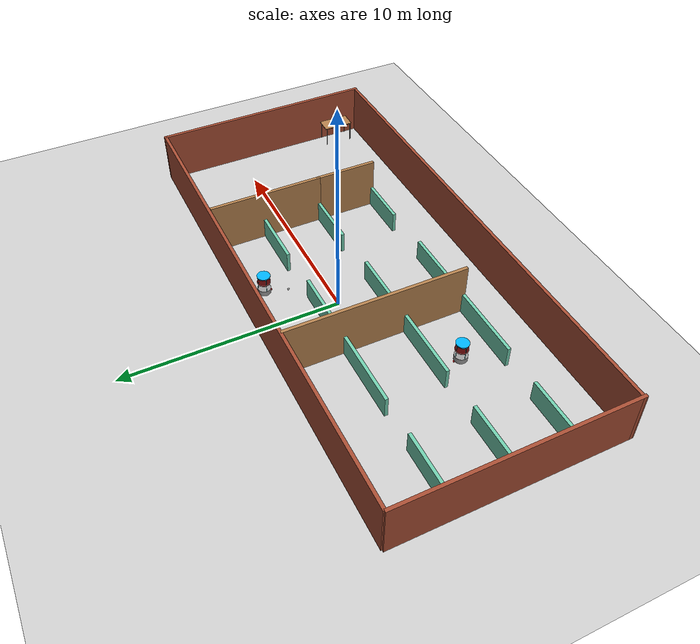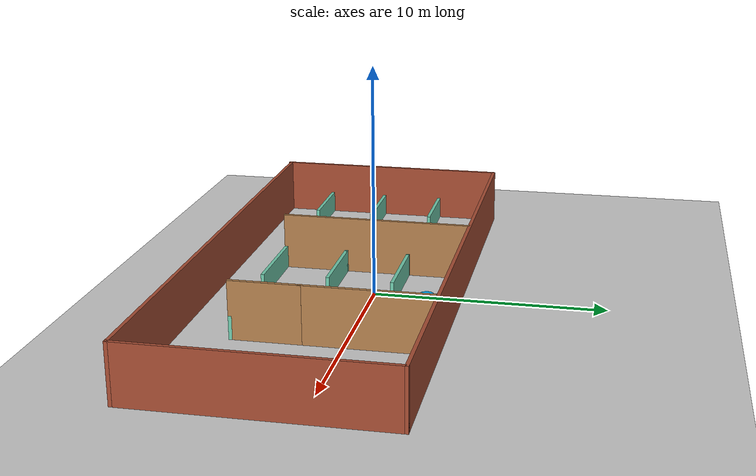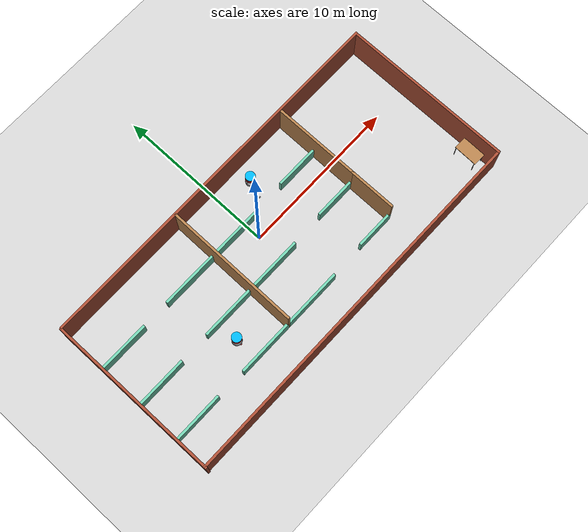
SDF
<sdf version="1.6">
 <world name="default">
  <plugin name="welcome_msg" filename="libhello.so"/>
  <light name="sun" type="directional">
   <pose>0 0 10 0 -0 0</pose>
   <diffuse>0.8 0.8 0.8 1</diffuse>
   <specular>0.2 0.2 0.2 1</specular>
   <attenuation>
    <range>1000</range>
    <constant>0.9</constant>
    <linear>0.01</linear>
    <quadratic>0.001</quadratic>
   </attenuation>
   <direction>-0.5 0.1 -0.9</direction>
  </light>
  <model name="ground_plane">
   <static>1</static>
   <link name="link">
    <collision name="collision">
     <geometry><plane><normal>0 0 1</normal><size>100 100</size></plane></geometry>
     <surface><friction><ode><mu>100</mu><mu2>50</mu2></ode></friction></surface>
    </collision>
    <visual name="visual">
     <cast_shadows>0</cast_shadows>
     <geometry><plane><normal>0 0 1</normal><size>100 100</size></plane></geometry>
     <material>
      <script><uri>file://media/materials/scripts/gazebo.material</uri><name>Gazebo/Grey</name></script>
     </material>
    </visual>
   </link>
  </model>
  <gravity>0 0 -9.8</gravity>
  <magnetic_field>6e-06 2.3e-05 -4.2e-05</magnetic_field>
  <atmosphere type="adiabatic"/>
  <physics name="default_physics" default="0" type="ode">
   <max_step_size>0.001</max_step_size>
   <real_time_factor>1</real_time_factor>
   <real_time_update_rate>1000</real_time_update_rate>
  </physics>
  <scene><ambient>0.4 0.4 0.4 1</ambient><background>0.7 0.7 0.7 1</background><shadows>1</shadows></scene>
  <spherical_coordinates>
   <surface_model>EARTH_WGS84</surface_model>
   <latitude_deg>0</latitude_deg>
   <longitude_deg>0</longitude_deg>
   <elevation>0</elevation>
   <heading_deg>0</heading_deg>
  </spherical_coordinates>
  <model name="restaurants">
   <link name="Wall_17">
    <pose>5.31564 2.50892 0 0 -0 1.57072</pose>
    <visual name="Wall_17_Visual">
     <pose>0 0 1.25 0 -0 0</pose>
     <geometry><box><size>5.45915 0.15 2.5</size></box></geometry>
     <material>
      <script><uri>file://media/materials/scripts/gazebo.material</uri><name>Gazebo/Wood</name></script>
      <ambient>1 1 1 1</ambient>
      <shader type="pixel"/>
      <diffuse>1 1 1 1</diffuse>
      <specular>0.2 0.2 0.2 1</specular>
      <emissive>0 0 0 1</emissive>
     </material>
     <meta><layer>0</layer></meta>
    </visual>
    <collision name="Wall_17_Collision">
     <pose>0 0 1.25 0 -0 0</pose>
     <geometry><box><size>5.45915 0.15 2.5</size></box></geometry>
     <surface>
      <friction>
       <ode><mu>1</mu><mu2>1</mu2><fdir1>0 0 0</fdir1><slip1>0</slip1><slip2>0</slip2></ode>
       <torsional>
        <coefficient>1</coefficient>
        <patch_radius>0</patch_radius>
        <surface_radius>0</surface_radius>
        <use_patch_radius>1</use_patch_radius>
        <ode><slip>0</slip></ode>
       </torsional>
      </friction>
      <bounce><restitution_coefficient>0</restitution_coefficient><threshold>1e+06</threshold></bounce>
      <contact>
       <collide_without_contact>0</collide_without_contact>
       <collide_without_contact_bitmask>1</collide_without_contact_bitmask>
       <collide_bitmask>1</collide_bitmask>
       <ode>
        <soft_cfm>0</soft_cfm>
        <soft_erp>0.2</soft_erp>
        <kp>1e+13</kp>
        <kd>1</kd>
        <max_vel>0.01</max_vel>
        <min_depth>0</min_depth>
       </ode>
       <bullet>
        <split_impulse>1</split_impulse>
        <split_impulse_penetration_threshold>-0.01</split_impulse_penetration_threshold>
        <soft_cfm>0</soft_cfm>
        <soft_erp>0.2</soft_erp>
        <kp>1e+13</kp>
        <kd>1</kd>
       </bullet>
      </contact>
     </surface>
    </collision>
   </link>
   <link name="Wall_19">
    <pose>5.31545 -1.57066 0 0 0 -1.5708</pose>
    <visual name="Wall_19_Visual">
     <pose>0 0 1.25 0 -0 0</pose>
     <geometry><box><size>3 0.15 2.5</size></box></geometry>
     <material>
      <script><uri>file://media/materials/scripts/gazebo.material</uri><name>Gazebo/Wood</name></script>
      <ambient>1 1 1 1</ambient>
      <shader type="pixel"/>
      <diffuse>1 1 1 1</diffuse>
      <specular>0.2 0.2 0.2 1</specular>
      <emissive>0 0 0 1</emissive>
     </material>
     <meta><layer>0</layer></meta>
    </visual>
    <collision name="Wall_19_Collision">
     <pose>0 0 1.25 0 -0 0</pose>
     <geometry><box><size>3 0.15 2.5</size></box></geometry>
     <surface>
      <friction>
       <ode><mu>1</mu><mu2>1</mu2><fdir1>0 0 0</fdir1><slip1>0</slip1><slip2>0</slip2></ode>
       <torsional>
        <coefficient>1</coefficient>
        <patch_radius>0</patch_radius>
        <surface_radius>0</surface_radius>
        <use_patch_radius>1</use_patch_radius>
        <ode><slip>0</slip></ode>
       </torsional>
      </friction>
      <bounce><restitution_coefficient>0</restitution_coefficient><threshold>1e+06</threshold></bounce>
      <contact>
       <collide_without_contact>0</collide_without_contact>
       <collide_without_contact_bitmask>1</collide_without_contact_bitmask>
       <collide_bitmask>1</collide_bitmask>
       <ode>
        <soft_cfm>0</soft_cfm>
        <soft_erp>0.2</soft_erp>
        <kp>1e+13</kp>
        <kd>1</kd>
        <max_vel>0.01</max_vel>
        <min_depth>0</min_depth>
       </ode>
       <bullet>
        <split_impulse>1</split_impulse>
        <split_impulse_penetration_threshold>-0.01</split_impulse_penetration_threshold>
        <soft_cfm>0</soft_cfm>
        <soft_erp>0.2</soft_erp>
        <kp>1e+13</kp>
        <kd>1</kd>
       </bullet>
      </contact>
     </surface>
    </collision>
   </link>
   <link name="Wall_4">
    <pose>0.042334 5.32675 0 0 -0 0</pose>
    <visual name="Wall_4_Visual">
     <pose>0 0 1.25 0 -0 0</pose>
     <geometry><box><size>23.5 0.15 2.5</size></box></geometry>
     <material>
      <script><uri>file://media/materials/scripts/gazebo.material</uri><name>Gazebo/Bricks</name></script>
      <ambient>1 1 1 1</ambient>
      <shader type="pixel"/>
      <diffuse>1 1 1 1</diffuse>
      <specular>0.2 0.2 0.2 1</specular>
      <emissive>0 0 0 1</emissive>
     </material>
     <meta><layer>0</layer></meta>
    </visual>
    <collision name="Wall_4_Collision">
     <pose>0 0 1.25 0 -0 0</pose>
     <geometry><box><size>23.5 0.15 2.5</size></box></geometry>
     <surface>
      <friction>
       <ode><mu>1</mu><mu2>1</mu2><fdir1>0 0 0</fdir1><slip1>0</slip1><slip2>0</slip2></ode>
       <torsional>
        <coefficient>1</coefficient>
        <patch_radius>0</patch_radius>
        <surface_radius>0</surface_radius>
        <use_patch_radius>1</use_patch_radius>
        <ode><slip>0</slip></ode>
       </torsional>
      </friction>
      <bounce><restitution_coefficient>0</restitution_coefficient><threshold>1e+06</threshold></bounce>
      <contact>
       <collide_without_contact>0</collide_without_contact>
       <collide_without_contact_bitmask>1</collide_without_contact_bitmask>
       <collide_bitmask>1</collide_bitmask>
       <ode>
        <soft_cfm>0</soft_cfm>
        <soft_erp>0.2</soft_erp>
        <kp>1e+13</kp>
        <kd>1</kd>
        <max_vel>0.01</max_vel>
        <min_depth>0</min_depth>
       </ode>
       <bullet>
        <split_impulse>1</split_impulse>
        <split_impulse_penetration_threshold>-0.01</split_impulse_penetration_threshold>
        <soft_cfm>0</soft_cfm>
        <soft_erp>0.2</soft_erp>
        <kp>1e+13</kp>
        <kd>1</kd>
       </bullet>
      </contact>
     </surface>
    </collision>
   </link>
   <link name="Wall_48">
    <pose>-3.08222 1.07627 0 0 0 -1.57567</pose>
    <visual name="Wall_48_Visual">
     <pose>0 0 1.25 0 -0 0</pose>
     <geometry><box><size>8.5 0.15 2.5</size></box></geometry>
     <material>
      <script><uri>file://media/materials/scripts/gazebo.material</uri><name>Gazebo/Wood</name></script>
      <ambient>1 1 1 1</ambient>
      <shader type="pixel"/>
      <diffuse>1 1 1 1</diffuse>
      <specular>0.2 0.2 0.2 1</specular>
      <emissive>0 0 0 1</emissive>
     </material>
     <meta><layer>0</layer></meta>
    </visual>
    <collision name="Wall_48_Collision">
     <pose>0 0 1.25 0 -0 0</pose>
     <geometry><box><size>8.5 0.15 2.5</size></box></geometry>
     <surface>
      <friction>
       <ode><mu>1</mu><mu2>1</mu2><fdir1>0 0 0</fdir1><slip1>0</slip1><slip2>0</slip2></ode>
       <torsional>
        <coefficient>1</coefficient>
        <patch_radius>0</patch_radius>
        <surface_radius>0</surface_radius>
        <use_patch_radius>1</use_patch_radius>
        <ode><slip>0</slip></ode>
       </torsional>
      </friction>
      <bounce><restitution_coefficient>0</restitution_coefficient><threshold>1e+06</threshold></bounce>
      <contact>
       <collide_without_contact>0</collide_without_contact>
       <collide_without_contact_bitmask>1</collide_without_contact_bitmask>
       <collide_bitmask>1</collide_bitmask>
       <ode>
        <soft_cfm>0</soft_cfm>
        <soft_erp>0.2</soft_erp>
        <kp>1e+13</kp>
        <kd>1</kd>
        <max_vel>0.01</max_vel>
        <min_depth>0</min_depth>
       </ode>
       <bullet>
        <split_impulse>1</split_impulse>
        <split_impulse_penetration_threshold>-0.01</split_impulse_penetration_threshold>
        <soft_cfm>0</soft_cfm>
        <soft_erp>0.2</soft_erp>
        <kp>1e+13</kp>
        <kd>1</kd>
       </bullet>
      </contact>
     </surface>
    </collision>
   </link>
   <link name="Wall_6">
    <pose>11.7173 0.026751 0 0 0 -1.5708</pose>
    <visual name="Wall_6_Visual">
     <pose>0 0 1.25 0 -0 0</pose>
     <geometry><box><size>10.75 0.15 2.5</size></box></geometry>
     <material>
      <script><uri>file://media/materials/scripts/gazebo.material</uri><name>Gazebo/Bricks</name></script>
      <ambient>1 1 1 1</ambient>
      <shader type="pixel"/>
      <diffuse>1 1 1 1</diffuse>
      <specular>0.2 0.2 0.2 1</specular>
      <emissive>0 0 0 1</emissive>
     </material>
     <meta><layer>0</layer></meta>
    </visual>
    <collision name="Wall_6_Collision">
     <pose>0 0 1.25 0 -0 0</pose>
     <geometry><box><size>10.75 0.15 2.5</size></box></geometry>
     <surface>
      <friction>
       <ode><mu>1</mu><mu2>1</mu2><fdir1>0 0 0</fdir1><slip1>0</slip1><slip2>0</slip2></ode>
       <torsional>
        <coefficient>1</coefficient>
        <patch_radius>0</patch_radius>
        <surface_radius>0</surface_radius>
        <use_patch_radius>1</use_patch_radius>
        <ode><slip>0</slip></ode>
       </torsional>
      </friction>
      <bounce><restitution_coefficient>0</restitution_coefficient><threshold>1e+06</threshold></bounce>
      <contact>
       <collide_without_contact>0</collide_without_contact>
       <collide_without_contact_bitmask>1</collide_without_contact_bitmask>
       <collide_bitmask>1</collide_bitmask>
       <ode>
        <soft_cfm>0</soft_cfm>
        <soft_erp>0.2</soft_erp>
        <kp>1e+13</kp>
        <kd>1</kd>
        <max_vel>0.01</max_vel>
        <min_depth>0</min_depth>
       </ode>
       <bullet>
        <split_impulse>1</split_impulse>
        <split_impulse_penetration_threshold>-0.01</split_impulse_penetration_threshold>
        <soft_cfm>0</soft_cfm>
        <soft_erp>0.2</soft_erp>
        <kp>1e+13</kp>
        <kd>1</kd>
       </bullet>
      </contact>
     </surface>
    </collision>
   </link>
   <link name="Wall_66">
    <pose>-10.1176 2.54034 0 0 -0 0</pose>
    <visual name="Wall_66_Visual">
     <pose>0 0 0.5 0 -0 0</pose>
     <geometry><box><size>3.25 0.15 1</size></box></geometry>
     <material>
      <script><uri>file://media/materials/scripts/gazebo.material</uri><name>Gazebo/Grey</name></script>
      <ambient>0.435294 0.796078 0.67451 1</ambient>
      <shader type="pixel"/>
      <diffuse>0.7 0.7 0.7 1</diffuse>
      <specular>0.01 0.01 0.01 1</specular>
      <emissive>0 0 0 1</emissive>
     </material>
     <meta><layer>0</layer></meta>
    </visual>
    <collision name="Wall_66_Collision">
     <pose>0 0 0.5 0 -0 0</pose>
     <geometry><box><size>3.25 0.15 1</size></box></geometry>
     <surface>
      <friction>
       <ode><mu>1</mu><mu2>1</mu2><fdir1>0 0 0</fdir1><slip1>0</slip1><slip2>0</slip2></ode>
       <torsional>
        <coefficient>1</coefficient>
        <patch_radius>0</patch_radius>
        <surface_radius>0</surface_radius>
        <use_patch_radius>1</use_patch_radius>
        <ode><slip>0</slip></ode>
       </torsional>
      </friction>
      <bounce><restitution_coefficient>0</restitution_coefficient><threshold>1e+06</threshold></bounce>
      <contact>
       <collide_without_contact>0</collide_without_contact>
       <collide_without_contact_bitmask>1</collide_without_contact_bitmask>
       <collide_bitmask>1</collide_bitmask>
       <ode>
        <soft_cfm>0</soft_cfm>
        <soft_erp>0.2</soft_erp>
        <kp>1e+13</kp>
        <kd>1</kd>
        <max_vel>0.01</max_vel>
        <min_depth>0</min_depth>
       </ode>
       <bullet>
        <split_impulse>1</split_impulse>
        <split_impulse_penetration_threshold>-0.01</split_impulse_penetration_threshold>
        <soft_cfm>0</soft_cfm>
        <soft_erp>0.2</soft_erp>
        <kp>1e+13</kp>
        <kd>1</kd>
       </bullet>
      </contact>
     </surface>
    </collision>
   </link>
   <link name="Wall_69">
    <pose>-10.1046 -0.300662 0 0 -0 0</pose>
    <visual name="Wall_69_Visual">
     <pose>0 0 0.5 0 -0 0</pose>
     <geometry><box><size>3.25 0.15 1</size></box></geometry>
     <material>
      <script><uri>file://media/materials/scripts/gazebo.material</uri><name>Gazebo/Grey</name></script>
      <ambient>0.435294 0.796078 0.67451 1</ambient>
      <shader type="pixel"/>
      <diffuse>0.7 0.7 0.7 1</diffuse>
      <specular>0.01 0.01 0.01 1</specular>
      <emissive>0 0 0 1</emissive>
     </material>
     <meta><layer>0</layer></meta>
    </visual>
    <collision name="Wall_69_Collision">
     <pose>0 0 0.5 0 -0 0</pose>
     <geometry><box><size>3.25 0.15 1</size></box></geometry>
     <surface>
      <friction>
       <ode><mu>1</mu><mu2>1</mu2><fdir1>0 0 0</fdir1><slip1>0</slip1><slip2>0</slip2></ode>
       <torsional>
        <coefficient>1</coefficient>
        <patch_radius>0</patch_radius>
        <surface_radius>0</surface_radius>
        <use_patch_radius>1</use_patch_radius>
        <ode><slip>0</slip></ode>
       </torsional>
      </friction>
      <bounce><restitution_coefficient>0</restitution_coefficient><threshold>1e+06</threshold></bounce>
      <contact>
       <collide_without_contact>0</collide_without_contact>
       <collide_without_contact_bitmask>1</collide_without_contact_bitmask>
       <collide_bitmask>1</collide_bitmask>
       <ode>
        <soft_cfm>0</soft_cfm>
        <soft_erp>0.2</soft_erp>
        <kp>1e+13</kp>
        <kd>1</kd>
        <max_vel>0.01</max_vel>
        <min_depth>0</min_depth>
       </ode>
       <bullet>
        <split_impulse>1</split_impulse>
        <split_impulse_penetration_threshold>-0.01</split_impulse_penetration_threshold>
        <soft_cfm>0</soft_cfm>
        <soft_erp>0.2</soft_erp>
        <kp>1e+13</kp>
        <kd>1</kd>
       </bullet>
      </contact>
     </surface>
    </collision>
   </link>
   <link name="Wall_7">
    <pose>0 -5.27325 0 0 -0 3.14159</pose>
    <visual name="Wall_7_Visual">
     <pose>0 0 1.25 0 -0 0</pose>
     <geometry><box><size>23.5847 0.15 2.5</size></box></geometry>
     <material>
      <script><uri>file://media/materials/scripts/gazebo.material</uri><name>Gazebo/Bricks</name></script>
      <ambient>1 1 1 1</ambient>
      <shader type="pixel"/>
      <diffuse>1 1 1 1</diffuse>
      <specular>0.2 0.2 0.2 1</specular>
      <emissive>0 0 0 1</emissive>
     </material>
     <meta><layer>0</layer></meta>
    </visual>
    <collision name="Wall_7_Collision">
     <pose>0 0 1.25 0 -0 0</pose>
     <geometry><box><size>23.5847 0.15 2.5</size></box></geometry>
     <surface>
      <friction>
       <ode><mu>1</mu><mu2>1</mu2><fdir1>0 0 0</fdir1><slip1>0</slip1><slip2>0</slip2></ode>
       <torsional>
        <coefficient>1</coefficient>
        <patch_radius>0</patch_radius>
        <surface_radius>0</surface_radius>
        <use_patch_radius>1</use_patch_radius>
        <ode><slip>0</slip></ode>
       </torsional>
      </friction>
      <bounce><restitution_coefficient>0</restitution_coefficient><threshold>1e+06</threshold></bounce>
      <contact>
       <collide_without_contact>0</collide_without_contact>
       <collide_without_contact_bitmask>1</collide_without_contact_bitmask>
       <collide_bitmask>1</collide_bitmask>
       <ode>
        <soft_cfm>0</soft_cfm>
        <soft_erp>0.2</soft_erp>
        <kp>1e+13</kp>
        <kd>1</kd>
        <max_vel>0.01</max_vel>
        <min_depth>0</min_depth>
       </ode>
       <bullet>
        <split_impulse>1</split_impulse>
        <split_impulse_penetration_threshold>-0.01</split_impulse_penetration_threshold>
        <soft_cfm>0</soft_cfm>
        <soft_erp>0.2</soft_erp>
        <kp>1e+13</kp>
        <kd>1</kd>
       </bullet>
      </contact>
     </surface>
    </collision>
   </link>
   <link name="Wall_71">
    <pose>-10.1406 -3.04466 0 0 -0 0</pose>
    <visual name="Wall_71_Visual">
     <pose>0 0 0.5 0 -0 0</pose>
     <geometry><box><size>3.25 0.15 1</size></box></geometry>
     <material>
      <script><uri>file://media/materials/scripts/gazebo.material</uri><name>Gazebo/Grey</name></script>
      <ambient>0.435294 0.796078 0.67451 1</ambient>
      <shader type="pixel"/>
      <diffuse>0.7 0.7 0.7 1</diffuse>
      <specular>0.01 0.01 0.01 1</specular>
      <emissive>0 0 0 1</emissive>
     </material>
     <meta><layer>0</layer></meta>
    </visual>
    <collision name="Wall_71_Collision">
     <pose>0 0 0.5 0 -0 0</pose>
     <geometry><box><size>3.25 0.15 1</size></box></geometry>
     <surface>
      <friction>
       <ode><mu>1</mu><mu2>1</mu2><fdir1>0 0 0</fdir1><slip1>0</slip1><slip2>0</slip2></ode>
       <torsional>
        <coefficient>1</coefficient>
        <patch_radius>0</patch_radius>
        <surface_radius>0</surface_radius>
        <use_patch_radius>1</use_patch_radius>
        <ode><slip>0</slip></ode>
       </torsional>
      </friction>
      <bounce><restitution_coefficient>0</restitution_coefficient><threshold>1e+06</threshold></bounce>
      <contact>
       <collide_without_contact>0</collide_without_contact>
       <collide_without_contact_bitmask>1</collide_without_contact_bitmask>
       <collide_bitmask>1</collide_bitmask>
       <ode>
        <soft_cfm>0</soft_cfm>
        <soft_erp>0.2</soft_erp>
        <kp>1e+13</kp>
        <kd>1</kd>
        <max_vel>0.01</max_vel>
        <min_depth>0</min_depth>
       </ode>
       <bullet>
        <split_impulse>1</split_impulse>
        <split_impulse_penetration_threshold>-0.01</split_impulse_penetration_threshold>
        <soft_cfm>0</soft_cfm>
        <soft_erp>0.2</soft_erp>
        <kp>1e+13</kp>
        <kd>1</kd>
       </bullet>
      </contact>
     </surface>
    </collision>
   </link>
   <link name="Wall_73">
    <pose>-4.76086 2.55834 0 0 -0 0</pose>
    <visual name="Wall_73_Visual">
     <pose>0 0 0.5 0 -0 0</pose>
     <geometry><box><size>3.98261 0.15 1</size></box></geometry>
     <material>
      <script><uri>file://media/materials/scripts/gazebo.material</uri><name>Gazebo/Grey</name></script>
      <ambient>0.435294 0.796078 0.67451 1</ambient>
      <shader type="pixel"/>
      <diffuse>0.7 0.7 0.7 1</diffuse>
      <specular>0.01 0.01 0.01 1</specular>
      <emissive>0 0 0 1</emissive>
     </material>
     <meta><layer>0</layer></meta>
    </visual>
    <collision name="Wall_73_Collision">
     <pose>0 0 0.5 0 -0 0</pose>
     <geometry><box><size>3.98261 0.15 1</size></box></geometry>
     <surface>
      <friction>
       <ode><mu>1</mu><mu2>1</mu2><fdir1>0 0 0</fdir1><slip1>0</slip1><slip2>0</slip2></ode>
       <torsional>
        <coefficient>1</coefficient>
        <patch_radius>0</patch_radius>
        <surface_radius>0</surface_radius>
        <use_patch_radius>1</use_patch_radius>
        <ode><slip>0</slip></ode>
       </torsional>
      </friction>
      <bounce><restitution_coefficient>0</restitution_coefficient><threshold>1e+06</threshold></bounce>
      <contact>
       <collide_without_contact>0</collide_without_contact>
       <collide_without_contact_bitmask>1</collide_without_contact_bitmask>
       <collide_bitmask>1</collide_bitmask>
       <ode>
        <soft_cfm>0</soft_cfm>
        <soft_erp>0.2</soft_erp>
        <kp>1e+13</kp>
        <kd>1</kd>
        <max_vel>0.01</max_vel>
        <min_depth>0</min_depth>
       </ode>
       <bullet>
        <split_impulse>1</split_impulse>
        <split_impulse_penetration_threshold>-0.01</split_impulse_penetration_threshold>
        <soft_cfm>0</soft_cfm>
        <soft_erp>0.2</soft_erp>
        <kp>1e+13</kp>
        <kd>1</kd>
       </bullet>
      </contact>
     </surface>
    </collision>
   </link>
   <link name="Wall_75">
    <pose>-4.69255 -0.273662 0 0 -0 0</pose>
    <visual name="Wall_75_Visual">
     <pose>0 0 0.5 0 -0 0</pose>
     <geometry><box><size>3.75 0.15 1</size></box></geometry>
     <material>
      <script><uri>file://media/materials/scripts/gazebo.material</uri><name>Gazebo/Grey</name></script>
      <ambient>0.435294 0.796078 0.67451 1</ambient>
      <shader type="pixel"/>
      <diffuse>0.7 0.7 0.7 1</diffuse>
      <specular>0.01 0.01 0.01 1</specular>
      <emissive>0 0 0 1</emissive>
     </material>
     <meta><layer>0</layer></meta>
    </visual>
    <collision name="Wall_75_Collision">
     <pose>0 0 0.5 0 -0 0</pose>
     <geometry><box><size>3.75 0.15 1</size></box></geometry>
     <surface>
      <friction>
       <ode><mu>1</mu><mu2>1</mu2><fdir1>0 0 0</fdir1><slip1>0</slip1><slip2>0</slip2></ode>
       <torsional>
        <coefficient>1</coefficient>
        <patch_radius>0</patch_radius>
        <surface_radius>0</surface_radius>
        <use_patch_radius>1</use_patch_radius>
        <ode><slip>0</slip></ode>
       </torsional>
      </friction>
      <bounce><restitution_coefficient>0</restitution_coefficient><threshold>1e+06</threshold></bounce>
      <contact>
       <collide_without_contact>0</collide_without_contact>
       <collide_without_contact_bitmask>1</collide_without_contact_bitmask>
       <collide_bitmask>1</collide_bitmask>
       <ode>
        <soft_cfm>0</soft_cfm>
        <soft_erp>0.2</soft_erp>
        <kp>1e+13</kp>
        <kd>1</kd>
        <max_vel>0.01</max_vel>
        <min_depth>0</min_depth>
       </ode>
       <bullet>
        <split_impulse>1</split_impulse>
        <split_impulse_penetration_threshold>-0.01</split_impulse_penetration_threshold>
        <soft_cfm>0</soft_cfm>
        <soft_erp>0.2</soft_erp>
        <kp>1e+13</kp>
        <kd>1</kd>
       </bullet>
      </contact>
     </surface>
    </collision>
   </link>
   <link name="Wall_79">
    <pose>-4.84555 -3.09866 0 0 -0 3.14159</pose>
    <visual name="Wall_79_Visual">
     <pose>0 0 0.5 0 -0 0</pose>
     <geometry><box><size>3.6359 0.15 1</size></box></geometry>
     <material>
      <script><uri>file://media/materials/scripts/gazebo.material</uri><name>Gazebo/Grey</name></script>
      <ambient>0.435294 0.796078 0.67451 1</ambient>
      <shader type="pixel"/>
      <diffuse>0.7 0.7 0.7 1</diffuse>
      <specular>0.01 0.01 0.01 1</specular>
      <emissive>0 0 0 1</emissive>
     </material>
     <meta><layer>0</layer></meta>
    </visual>
    <collision name="Wall_79_Collision">
     <pose>0 0 0.5 0 -0 0</pose>
     <geometry><box><size>3.6359 0.15 1</size></box></geometry>
     <surface>
      <friction>
       <ode><mu>1</mu><mu2>1</mu2><fdir1>0 0 0</fdir1><slip1>0</slip1><slip2>0</slip2></ode>
       <torsional>
        <coefficient>1</coefficient>
        <patch_radius>0</patch_radius>
        <surface_radius>0</surface_radius>
        <use_patch_radius>1</use_patch_radius>
        <ode><slip>0</slip></ode>
       </torsional>
      </friction>
      <bounce><restitution_coefficient>0</restitution_coefficient><threshold>1e+06</threshold></bounce>
      <contact>
       <collide_without_contact>0</collide_without_contact>
       <collide_without_contact_bitmask>1</collide_without_contact_bitmask>
       <collide_bitmask>1</collide_bitmask>
       <ode>
        <soft_cfm>0</soft_cfm>
        <soft_erp>0.2</soft_erp>
        <kp>1e+13</kp>
        <kd>1</kd>
        <max_vel>0.01</max_vel>
        <min_depth>0</min_depth>
       </ode>
       <bullet>
        <split_impulse>1</split_impulse>
        <split_impulse_penetration_threshold>-0.01</split_impulse_penetration_threshold>
        <soft_cfm>0</soft_cfm>
        <soft_erp>0.2</soft_erp>
        <kp>1e+13</kp>
        <kd>1</kd>
       </bullet>
      </contact>
     </surface>
    </collision>
   </link>
   <link name="Wall_8">
    <pose>-11.7173 -0.026751 0 0 -0 1.5708</pose>
    <visual name="Wall_8_Visual">
     <pose>0 0 1.25 0 -0 0</pose>
     <geometry><box><size>10.75 0.15 2.5</size></box></geometry>
     <material>
      <script><uri>file://media/materials/scripts/gazebo.material</uri><name>Gazebo/Bricks</name></script>
      <ambient>1 1 1 1</ambient>
      <shader type="pixel"/>
      <diffuse>1 1 1 1</diffuse>
      <specular>0.2 0.2 0.2 1</specular>
      <emissive>0 0 0 1</emissive>
     </material>
     <meta><layer>0</layer></meta>
    </visual>
    <collision name="Wall_8_Collision">
     <pose>0 0 1.25 0 -0 0</pose>
     <geometry><box><size>10.75 0.15 2.5</size></box></geometry>
     <surface>
      <friction>
       <ode><mu>1</mu><mu2>1</mu2><fdir1>0 0 0</fdir1><slip1>0</slip1><slip2>0</slip2></ode>
       <torsional>
        <coefficient>1</coefficient>
        <patch_radius>0</patch_radius>
        <surface_radius>0</surface_radius>
        <use_patch_radius>1</use_patch_radius>
        <ode><slip>0</slip></ode>
       </torsional>
      </friction>
      <bounce><restitution_coefficient>0</restitution_coefficient><threshold>1e+06</threshold></bounce>
      <contact>
       <collide_without_contact>0</collide_without_contact>
       <collide_without_contact_bitmask>1</collide_without_contact_bitmask>
       <collide_bitmask>1</collide_bitmask>
       <ode>
        <soft_cfm>0</soft_cfm>
        <soft_erp>0.2</soft_erp>
        <kp>1e+13</kp>
        <kd>1</kd>
        <max_vel>0.01</max_vel>
        <min_depth>0</min_depth>
       </ode>
       <bullet>
        <split_impulse>1</split_impulse>
        <split_impulse_penetration_threshold>-0.01</split_impulse_penetration_threshold>
        <soft_cfm>0</soft_cfm>
        <soft_erp>0.2</soft_erp>
        <kp>1e+13</kp>
        <kd>1</kd>
       </bullet>
      </contact>
     </surface>
    </collision>
   </link>
   <link name="Wall_81">
    <pose>-1.16955 2.55834 0 0 -0 0</pose>
    <visual name="Wall_81_Visual">
     <pose>0 0 0.5 0 -0 0</pose>
     <geometry><box><size>3.5 0.15 1</size></box></geometry>
     <material>
      <script><uri>file://media/materials/scripts/gazebo.material</uri><name>Gazebo/Grey</name></script>
      <ambient>0.435294 0.796078 0.67451 1</ambient>
      <shader type="pixel"/>
      <diffuse>0.7 0.7 0.7 1</diffuse>
      <specular>0.01 0.01 0.01 1</specular>
      <emissive>0 0 0 1</emissive>
     </material>
     <meta><layer>0</layer></meta>
    </visual>
    <collision name="Wall_81_Collision">
     <pose>0 0 0.5 0 -0 0</pose>
     <geometry><box><size>3.5 0.15 1</size></box></geometry>
     <surface>
      <friction>
       <ode><mu>1</mu><mu2>1</mu2><fdir1>0 0 0</fdir1><slip1>0</slip1><slip2>0</slip2></ode>
       <torsional>
        <coefficient>1</coefficient>
        <patch_radius>0</patch_radius>
        <surface_radius>0</surface_radius>
        <use_patch_radius>1</use_patch_radius>
        <ode><slip>0</slip></ode>
       </torsional>
      </friction>
      <bounce><restitution_coefficient>0</restitution_coefficient><threshold>1e+06</threshold></bounce>
      <contact>
       <collide_without_contact>0</collide_without_contact>
       <collide_without_contact_bitmask>1</collide_without_contact_bitmask>
       <collide_bitmask>1</collide_bitmask>
       <ode>
        <soft_cfm>0</soft_cfm>
        <soft_erp>0.2</soft_erp>
        <kp>1e+13</kp>
        <kd>1</kd>
        <max_vel>0.01</max_vel>
        <min_depth>0</min_depth>
       </ode>
       <bullet>
        <split_impulse>1</split_impulse>
        <split_impulse_penetration_threshold>-0.01</split_impulse_penetration_threshold>
        <soft_cfm>0</soft_cfm>
        <soft_erp>0.2</soft_erp>
        <kp>1e+13</kp>
        <kd>1</kd>
       </bullet>
      </contact>
     </surface>
    </collision>
   </link>
   <link name="Wall_83">
    <pose>-1.21755 -0.273662 0 0 -0 0</pose>
    <visual name="Wall_83_Visual">
     <pose>0 0 0.5 0 -0 0</pose>
     <geometry><box><size>3.5 0.15 1</size></box></geometry>
     <material>
      <script><uri>file://media/materials/scripts/gazebo.material</uri><name>Gazebo/Grey</name></script>
      <ambient>0.435294 0.796078 0.67451 1</ambient>
      <shader type="pixel"/>
      <diffuse>0.7 0.7 0.7 1</diffuse>
      <specular>0.01 0.01 0.01 1</specular>
      <emissive>0 0 0 1</emissive>
     </material>
     <meta><layer>0</layer></meta>
    </visual>
    <collision name="Wall_83_Collision">
     <pose>0 0 0.5 0 -0 0</pose>
     <geometry><box><size>3.5 0.15 1</size></box></geometry>
     <surface>
      <friction>
       <ode><mu>1</mu><mu2>1</mu2><fdir1>0 0 0</fdir1><slip1>0</slip1><slip2>0</slip2></ode>
       <torsional>
        <coefficient>1</coefficient>
        <patch_radius>0</patch_radius>
        <surface_radius>0</surface_radius>
        <use_patch_radius>1</use_patch_radius>
        <ode><slip>0</slip></ode>
       </torsional>
      </friction>
      <bounce><restitution_coefficient>0</restitution_coefficient><threshold>1e+06</threshold></bounce>
      <contact>
       <collide_without_contact>0</collide_without_contact>
       <collide_without_contact_bitmask>1</collide_without_contact_bitmask>
       <collide_bitmask>1</collide_bitmask>
       <ode>
        <soft_cfm>0</soft_cfm>
        <soft_erp>0.2</soft_erp>
        <kp>1e+13</kp>
        <kd>1</kd>
        <max_vel>0.01</max_vel>
        <min_depth>0</min_depth>
       </ode>
       <bullet>
        <split_impulse>1</split_impulse>
        <split_impulse_penetration_threshold>-0.01</split_impulse_penetration_threshold>
        <soft_cfm>0</soft_cfm>
        <soft_erp>0.2</soft_erp>
        <kp>1e+13</kp>
        <kd>1</kd>
       </bullet>
      </contact>
     </surface>
    </collision>
   </link>
   <link name="Wall_85">
    <pose>-1.24555 -3.09866 0 0 -0 0</pose>
    <visual name="Wall_85_Visual">
     <pose>0 0 0.5 0 -0 0</pose>
     <geometry><box><size>3.8641 0.15 1</size></box></geometry>
     <material>
      <script><uri>file://media/materials/scripts/gazebo.material</uri><name>Gazebo/Grey</name></script>
      <ambient>0.435294 0.796078 0.67451 1</ambient>
      <shader type="pixel"/>
      <diffuse>0.7 0.7 0.7 1</diffuse>
      <specular>0.01 0.01 0.01 1</specular>
      <emissive>0 0 0 1</emissive>
     </material>
     <meta><layer>0</layer></meta>
    </visual>
    <collision name="Wall_85_Collision">
     <pose>0 0 0.5 0 -0 0</pose>
     <geometry><box><size>3.8641 0.15 1</size></box></geometry>
     <surface>
      <friction>
       <ode><mu>1</mu><mu2>1</mu2><fdir1>0 0 0</fdir1><slip1>0</slip1><slip2>0</slip2></ode>
       <torsional>
        <coefficient>1</coefficient>
        <patch_radius>0</patch_radius>
        <surface_radius>0</surface_radius>
        <use_patch_radius>1</use_patch_radius>
        <ode><slip>0</slip></ode>
       </torsional>
      </friction>
      <bounce><restitution_coefficient>0</restitution_coefficient><threshold>1e+06</threshold></bounce>
      <contact>
       <collide_without_contact>0</collide_without_contact>
       <collide_without_contact_bitmask>1</collide_without_contact_bitmask>
       <collide_bitmask>1</collide_bitmask>
       <ode>
        <soft_cfm>0</soft_cfm>
        <soft_erp>0.2</soft_erp>
        <kp>1e+13</kp>
        <kd>1</kd>
        <max_vel>0.01</max_vel>
        <min_depth>0</min_depth>
       </ode>
       <bullet>
        <split_impulse>1</split_impulse>
        <split_impulse_penetration_threshold>-0.01</split_impulse_penetration_threshold>
        <soft_cfm>0</soft_cfm>
        <soft_erp>0.2</soft_erp>
        <kp>1e+13</kp>
        <kd>1</kd>
       </bullet>
      </contact>
     </surface>
    </collision>
   </link>
   <link name="Wall_87">
    <pose>3.86945 2.67934 0 0 -0 0</pose>
    <visual name="Wall_87_Visual">
     <pose>0 0 0.5 0 -0 0</pose>
     <geometry><box><size>2.75 0.15 1</size></box></geometry>
     <material>
      <script><uri>file://media/materials/scripts/gazebo.material</uri><name>Gazebo/Grey</name></script>
      <ambient>0.435294 0.796078 0.67451 1</ambient>
      <shader type="pixel"/>
      <diffuse>0.7 0.7 0.7 1</diffuse>
      <specular>0.01 0.01 0.01 1</specular>
      <emissive>0 0 0 1</emissive>
     </material>
     <meta><layer>0</layer></meta>
    </visual>
    <collision name="Wall_87_Collision">
     <pose>0 0 0.5 0 -0 0</pose>
     <geometry><box><size>2.75 0.15 1</size></box></geometry>
     <surface>
      <friction>
       <ode><mu>1</mu><mu2>1</mu2><fdir1>0 0 0</fdir1><slip1>0</slip1><slip2>0</slip2></ode>
       <torsional>
        <coefficient>1</coefficient>
        <patch_radius>0</patch_radius>
        <surface_radius>0</surface_radius>
        <use_patch_radius>1</use_patch_radius>
        <ode><slip>0</slip></ode>
       </torsional>
      </friction>
      <bounce><restitution_coefficient>0</restitution_coefficient><threshold>1e+06</threshold></bounce>
      <contact>
       <collide_without_contact>0</collide_without_contact>
       <collide_without_contact_bitmask>1</collide_without_contact_bitmask>
       <collide_bitmask>1</collide_bitmask>
       <ode>
        <soft_cfm>0</soft_cfm>
        <soft_erp>0.2</soft_erp>
        <kp>1e+13</kp>
        <kd>1</kd>
        <max_vel>0.01</max_vel>
        <min_depth>0</min_depth>
       </ode>
       <bullet>
        <split_impulse>1</split_impulse>
        <split_impulse_penetration_threshold>-0.01</split_impulse_penetration_threshold>
        <soft_cfm>0</soft_cfm>
        <soft_erp>0.2</soft_erp>
        <kp>1e+13</kp>
        <kd>1</kd>
       </bullet>
      </contact>
     </surface>
    </collision>
   </link>
   <link name="Wall_92">
    <pose>4.01545 -0.145661 0 0 -0 3.14159</pose>
    <visual name="Wall_92_Visual">
     <pose>0 0 0.5 0 -0 0</pose>
     <geometry><box><size>2.75 0.15 1</size></box></geometry>
     <material>
      <script><uri>file://media/materials/scripts/gazebo.material</uri><name>Gazebo/Grey</name></script>
      <ambient>0.435294 0.796078 0.67451 1</ambient>
      <shader type="pixel"/>
      <diffuse>0.7 0.7 0.7 1</diffuse>
      <specular>0.01 0.01 0.01 1</specular>
      <emissive>0 0 0 1</emissive>
     </material>
     <meta><layer>0</layer></meta>
    </visual>
    <collision name="Wall_92_Collision">
     <pose>0 0 0.5 0 -0 0</pose>
     <geometry><box><size>2.75 0.15 1</size></box></geometry>
     <surface>
      <friction>
       <ode><mu>1</mu><mu2>1</mu2><fdir1>0 0 0</fdir1><slip1>0</slip1><slip2>0</slip2></ode>
       <torsional>
        <coefficient>1</coefficient>
        <patch_radius>0</patch_radius>
        <surface_radius>0</surface_radius>
        <use_patch_radius>1</use_patch_radius>
        <ode><slip>0</slip></ode>
       </torsional>
      </friction>
      <bounce><restitution_coefficient>0</restitution_coefficient><threshold>1e+06</threshold></bounce>
      <contact>
       <collide_without_contact>0</collide_without_contact>
       <collide_without_contact_bitmask>1</collide_without_contact_bitmask>
       <collide_bitmask>1</collide_bitmask>
       <ode>
        <soft_cfm>0</soft_cfm>
        <soft_erp>0.2</soft_erp>
        <kp>1e+13</kp>
        <kd>1</kd>
        <max_vel>0.01</max_vel>
        <min_depth>0</min_depth>
       </ode>
       <bullet>
        <split_impulse>1</split_impulse>
        <split_impulse_penetration_threshold>-0.01</split_impulse_penetration_threshold>
        <soft_cfm>0</soft_cfm>
        <soft_erp>0.2</soft_erp>
        <kp>1e+13</kp>
        <kd>1</kd>
       </bullet>
      </contact>
     </surface>
    </collision>
   </link>
   <link name="Wall_94">
    <pose>4.14045 -2.99566 0 0 -0 3.14159</pose>
    <visual name="Wall_94_Visual">
     <pose>0 0 0.5 0 -0 0</pose>
     <geometry><box><size>2.5 0.15 1</size></box></geometry>
     <material>
      <script><uri>file://media/materials/scripts/gazebo.material</uri><name>Gazebo/Grey</name></script>
      <ambient>0.435294 0.796078 0.67451 1</ambient>
      <shader type="pixel"/>
      <diffuse>0.7 0.7 0.7 1</diffuse>
      <specular>0.01 0.01 0.01 1</specular>
      <emissive>0 0 0 1</emissive>
     </material>
     <meta><layer>0</layer></meta>
    </visual>
    <collision name="Wall_94_Collision">
     <pose>0 0 0.5 0 -0 0</pose>
     <geometry><box><size>2.5 0.15 1</size></box></geometry>
     <surface>
      <friction>
       <ode><mu>1</mu><mu2>1</mu2><fdir1>0 0 0</fdir1><slip1>0</slip1><slip2>0</slip2></ode>
       <torsional>
        <coefficient>1</coefficient>
        <patch_radius>0</patch_radius>
        <surface_radius>0</surface_radius>
        <use_patch_radius>1</use_patch_radius>
        <ode><slip>0</slip></ode>
       </torsional>
      </friction>
      <bounce><restitution_coefficient>0</restitution_coefficient><threshold>1e+06</threshold></bounce>
      <contact>
       <collide_without_contact>0</collide_without_contact>
       <collide_without_contact_bitmask>1</collide_without_contact_bitmask>
       <collide_bitmask>1</collide_bitmask>
       <ode>
        <soft_cfm>0</soft_cfm>
        <soft_erp>0.2</soft_erp>
        <kp>1e+13</kp>
        <kd>1</kd>
        <max_vel>0.01</max_vel>
        <min_depth>0</min_depth>
       </ode>
       <bullet>
        <split_impulse>1</split_impulse>
        <split_impulse_penetration_threshold>-0.01</split_impulse_penetration_threshold>
        <soft_cfm>0</soft_cfm>
        <soft_erp>0.2</soft_erp>
        <kp>1e+13</kp>
        <kd>1</kd>
       </bullet>
      </contact>
     </surface>
    </collision>
   </link>
   <static>1</static>
   <pose>0.44296 -1.57393 0 0 -0 0</pose>
  </model>
  <model name="white_ball">
   <link name="link_0">
    <inertial>
     <mass>1</mass>
     <inertia><ixx>0.1</ixx><ixy>0</ixy><ixz>0</ixz><iyy>0.1</iyy><iyz>0</iyz><izz>0.1</izz></inertia>
    </inertial>
    <visual name="visual">
     <geometry><sphere><radius>0.05</radius></sphere></geometry>
     <material>
      <lighting>1</lighting>
      <script><uri>file://media/materials/scripts/gazebo.material</uri><name>Gazebo/Grey</name></script>
      <shader type="pixel"><normal_map>__default__</normal_map></shader>
      <ambient>1 1 1 1</ambient>
      <diffuse>1 1 1 1</diffuse>
      <specular>1 1 1 1</specular>
      <emissive>1 1 1 1</emissive>
     </material>
    </visual>
    <collision name="collision">
     <geometry><sphere><radius>0.05</radius></sphere></geometry>
     <surface>
      <friction>
       <ode><mu>1</mu><mu2>1</mu2><fdir1>0 0 0</fdir1><slip1>0</slip1><slip2>0</slip2></ode>
       <torsional>
        <coefficient>1</coefficient>
        <patch_radius>0</patch_radius>
        <surface_radius>0</surface_radius>
        <use_patch_radius>1</use_patch_radius>
        <ode><slip>0</slip></ode>
       </torsional>
      </friction>
      <bounce><restitution_coefficient>0</restitution_coefficient><threshold>1e+06</threshold></bounce>
      <contact>
       <collide_without_contact>0</collide_without_contact>
       <collide_without_contact_bitmask>1</collide_without_contact_bitmask>
       <collide_bitmask>1</collide_bitmask>
       <ode>
        <soft_cfm>0</soft_cfm>
        <soft_erp>0.2</soft_erp>
        <kp>1e+13</kp>
        <kd>1</kd>
        <max_vel>0.01</max_vel>
        <min_depth>0</min_depth>
       </ode>
       <bullet>
        <split_impulse>1</split_impulse>
        <split_impulse_penetration_threshold>-0.01</split_impulse_penetration_threshold>
        <soft_cfm>0</soft_cfm>
        <soft_erp>0.2</soft_erp>
        <kp>1e+13</kp>
        <kd>1</kd>
       </bullet>
      </contact>
     </surface>
    </collision>
   </link>
   <static>0</static>
   <pose>1.78974 1.63037 0.05 0 -0 0</pose>
  </model>
  <model name="DFRm2_final_clone_clone">
   <link name="link_0">
    <pose>0 0.027 0.6025 0 -0 0</pose>
    <inertial>
     <mass>1</mass>
     <inertia><ixx>0.145833</ixx><ixy>0</ixy><ixz>0</ixz><iyy>0.145833</iyy><iyz>0</iyz><izz>0.125</izz></inertia>
    </inertial>
    <visual name="visual">
     <geometry><cylinder><radius>0.3</radius><length>0.05</length></cylinder></geometry>
     <material>
      <lighting>1</lighting>
      <script><uri>file://media/materials/scripts/gazebo.material</uri><name>Gazebo/Grey</name></script>
      <shader type="pixel"><normal_map>__default__</normal_map></shader>
      <ambient>0 0 1 1</ambient>
      <diffuse>0 0.7 1 1</diffuse>
      <specular>0.01 0.01 1 1</specular>
      <emissive>0 0 0 1</emissive>
     </material>
    </visual>
    <collision name="collision">
     <geometry><cylinder><radius>0.3</radius><length>0.05</length></cylinder></geometry>
     <surface>
      <friction>
       <ode><mu>1</mu><mu2>1</mu2><fdir1>0 0 0</fdir1><slip1>0</slip1><slip2>0</slip2></ode>
       <torsional>
        <coefficient>1</coefficient>
        <patch_radius>0</patch_radius>
        <surface_radius>0</surface_radius>
        <use_patch_radius>1</use_patch_radius>
        <ode><slip>0</slip></ode>
       </torsional>
      </friction>
      <bounce><restitution_coefficient>0</restitution_coefficient><threshold>1e+06</threshold></bounce>
      <contact>
       <collide_without_contact>0</collide_without_contact>
       <collide_without_contact_bitmask>1</collide_without_contact_bitmask>
       <collide_bitmask>1</collide_bitmask>
       <ode>
        <soft_cfm>0</soft_cfm>
        <soft_erp>0.2</soft_erp>
        <kp>1e+13</kp>
        <kd>1</kd>
        <max_vel>0.01</max_vel>
        <min_depth>0</min_depth>
       </ode>
       <bullet>
        <split_impulse>1</split_impulse>
        <split_impulse_penetration_threshold>-0.01</split_impulse_penetration_threshold>
        <soft_cfm>0</soft_cfm>
        <soft_erp>0.2</soft_erp>
        <kp>1e+13</kp>
        <kd>1</kd>
       </bullet>
      </contact>
     </surface>
    </collision>
   </link>
   <link name="link_0_clone">
    <pose>-0 0.027 -0.2225 0 -0 0</pose>
    <inertial>
     <mass>1</mass>
     <inertia><ixx>0.145833</ixx><ixy>0</ixy><ixz>0</ixz><iyy>0.145833</iyy><iyz>0</iyz><izz>0.125</izz></inertia>
    </inertial>
    <visual name="visual">
     <geometry><cylinder><radius>0.3</radius><length>0.25</length></cylinder></geometry>
     <material>
      <lighting>1</lighting>
      <script><uri>file://media/materials/scripts/gazebo.material</uri><name>Gazebo/Grey</name></script>
      <shader type="pixel"><normal_map>__default__</normal_map></shader>
      <ambient>0.3 0.3 0.3 1</ambient>
      <diffuse>0.7 0.7 0.7 1</diffuse>
      <specular>0.01 0.01 0.01 1</specular>
      <emissive>0 0 0 1</emissive>
     </material>
    </visual>
    <collision name="collision">
     <geometry><cylinder><radius>0.3</radius><length>0.25</length></cylinder></geometry>
     <surface>
      <friction>
       <ode><mu>1</mu><mu2>1</mu2><fdir1>0 0 0</fdir1><slip1>0</slip1><slip2>0</slip2></ode>
       <torsional>
        <coefficient>1</coefficient>
        <patch_radius>0</patch_radius>
        <surface_radius>0</surface_radius>
        <use_patch_radius>1</use_patch_radius>
        <ode><slip>0</slip></ode>
       </torsional>
      </friction>
      <bounce><restitution_coefficient>0</restitution_coefficient><threshold>1e+06</threshold></bounce>
      <contact>
       <collide_without_contact>0</collide_without_contact>
       <collide_without_contact_bitmask>1</collide_without_contact_bitmask>
       <collide_bitmask>1</collide_bitmask>
       <ode>
        <soft_cfm>0</soft_cfm>
        <soft_erp>0.2</soft_erp>
        <kp>1e+13</kp>
        <kd>1</kd>
        <max_vel>0.01</max_vel>
        <min_depth>0</min_depth>
       </ode>
       <bullet>
        <split_impulse>1</split_impulse>
        <split_impulse_penetration_threshold>-0.01</split_impulse_penetration_threshold>
        <soft_cfm>0</soft_cfm>
        <soft_erp>0.2</soft_erp>
        <kp>1e+13</kp>
        <kd>1</kd>
       </bullet>
      </contact>
     </surface>
    </collision>
   </link>
   <link name="link_0_clone_0">
    <pose>-0 0.027 0.2525 0 -0 0</pose>
    <inertial>
     <mass>1</mass>
     <inertia><ixx>0.145833</ixx><ixy>0</ixy><ixz>0</ixz><iyy>0.145833</iyy><iyz>0</iyz><izz>0.125</izz></inertia>
    </inertial>
    <visual name="visual">
     <geometry><cylinder><radius>0.3</radius><length>0.05</length></cylinder></geometry>
     <material>
      <lighting>1</lighting>
      <script><uri>file://media/materials/scripts/gazebo.material</uri><name>Gazebo/Grey</name></script>
      <shader type="pixel"><normal_map>__default__</normal_map></shader>
      <ambient>0.3 0 0 0</ambient>
      <diffuse>0.7 0.7 0.7 1</diffuse>
      <specular>0.01 0.01 0.01 1</specular>
      <emissive>0 0 0 1</emissive>
     </material>
    </visual>
    <collision name="collision">
     <geometry><cylinder><radius>0.3</radius><length>0.05</length></cylinder></geometry>
     <surface>
      <friction>
       <ode><mu>1</mu><mu2>1</mu2><fdir1>0 0 0</fdir1><slip1>0</slip1><slip2>0</slip2></ode>
       <torsional>
        <coefficient>1</coefficient>
        <patch_radius>0</patch_radius>
        <surface_radius>0</surface_radius>
        <use_patch_radius>1</use_patch_radius>
        <ode><slip>0</slip></ode>
       </torsional>
      </friction>
      <bounce><restitution_coefficient>0</restitution_coefficient><threshold>1e+06</threshold></bounce>
      <contact>
       <collide_without_contact>0</collide_without_contact>
       <collide_without_contact_bitmask>1</collide_without_contact_bitmask>
       <collide_bitmask>1</collide_bitmask>
       <ode>
        <soft_cfm>0</soft_cfm>
        <soft_erp>0.2</soft_erp>
        <kp>1e+13</kp>
        <kd>1</kd>
        <max_vel>0.01</max_vel>
        <min_depth>0</min_depth>
       </ode>
       <bullet>
        <split_impulse>1</split_impulse>
        <split_impulse_penetration_threshold>-0.01</split_impulse_penetration_threshold>
        <soft_cfm>0</soft_cfm>
        <soft_erp>0.2</soft_erp>
        <kp>1e+13</kp>
        <kd>1</kd>
       </bullet>
      </contact>
     </surface>
    </collision>
   </link>
   <link name="link_1">
    <pose>-0.27 0.027 0.2525 0 -0 0</pose>
    <inertial>
     <mass>1</mass>
     <inertia><ixx>0.145833</ixx><ixy>0</ixy><ixz>0</ixz><iyy>0.145833</iyy><iyz>0</iyz><izz>0.125</izz></inertia>
    </inertial>
    <visual name="visual">
     <geometry><cylinder><radius>0.01</radius><length>0.72</length></cylinder></geometry>
     <material>
      <lighting>1</lighting>
      <script><uri>file://media/materials/scripts/gazebo.material</uri><name>Gazebo/Grey</name></script>
      <shader type="pixel"><normal_map>__default__</normal_map></shader>
      <ambient>0 0.3 0.3 1</ambient>
      <diffuse>0 0.7 0.7 1</diffuse>
      <specular>0 0.01 0.01 1</specular>
      <emissive>0 0 0 1</emissive>
     </material>
    </visual>
    <collision name="collision">
     <geometry><cylinder><radius>0.01</radius><length>0.72</length></cylinder></geometry>
     <surface>
      <friction>
       <ode><mu>1</mu><mu2>1</mu2><fdir1>0 0 0</fdir1><slip1>0</slip1><slip2>0</slip2></ode>
       <torsional>
        <coefficient>1</coefficient>
        <patch_radius>0</patch_radius>
        <surface_radius>0</surface_radius>
        <use_patch_radius>1</use_patch_radius>
        <ode><slip>0</slip></ode>
       </torsional>
      </friction>
      <bounce><restitution_coefficient>0</restitution_coefficient><threshold>1e+06</threshold></bounce>
      <contact>
       <collide_without_contact>0</collide_without_contact>
       <collide_without_contact_bitmask>1</collide_without_contact_bitmask>
       <collide_bitmask>1</collide_bitmask>
       <ode>
        <soft_cfm>0</soft_cfm>
        <soft_erp>0.2</soft_erp>
        <kp>1e+13</kp>
        <kd>1</kd>
        <max_vel>0.01</max_vel>
        <min_depth>0</min_depth>
       </ode>
       <bullet>
        <split_impulse>1</split_impulse>
        <split_impulse_penetration_threshold>-0.01</split_impulse_penetration_threshold>
        <soft_cfm>0</soft_cfm>
        <soft_erp>0.2</soft_erp>
        <kp>1e+13</kp>
        <kd>1</kd>
       </bullet>
      </contact>
     </surface>
    </collision>
   </link>
   <link name="link_1_clone">
    <pose>-0 -0.243 0.2525 0 -0 0</pose>
    <inertial>
     <mass>1</mass>
     <inertia><ixx>0.145833</ixx><ixy>0</ixy><ixz>0</ixz><iyy>0.145833</iyy><iyz>0</iyz><izz>0.125</izz></inertia>
    </inertial>
    <visual name="visual">
     <geometry><cylinder><radius>0.01</radius><length>0.72</length></cylinder></geometry>
     <material>
      <lighting>1</lighting>
      <script><uri>file://media/materials/scripts/gazebo.material</uri><name>Gazebo/Grey</name></script>
      <shader type="pixel"><normal_map>__default__</normal_map></shader>
      <ambient>0 0.3 0.3 1</ambient>
      <diffuse>0 0.7 0.7 1</diffuse>
      <specular>0 0.01 0.01 1</specular>
      <emissive>0 0 0 1</emissive>
     </material>
    </visual>
    <collision name="collision">
     <geometry><cylinder><radius>0.01</radius><length>0.72</length></cylinder></geometry>
     <surface>
      <friction>
       <ode><mu>1</mu><mu2>1</mu2><fdir1>0 0 0</fdir1><slip1>0</slip1><slip2>0</slip2></ode>
       <torsional>
        <coefficient>1</coefficient>
        <patch_radius>0</patch_radius>
        <surface_radius>0</surface_radius>
        <use_patch_radius>1</use_patch_radius>
        <ode><slip>0</slip></ode>
       </torsional>
      </friction>
      <bounce><restitution_coefficient>0</restitution_coefficient><threshold>1e+06</threshold></bounce>
      <contact>
       <collide_without_contact>0</collide_without_contact>
       <collide_without_contact_bitmask>1</collide_without_contact_bitmask>
       <collide_bitmask>1</collide_bitmask>
       <ode>
        <soft_cfm>0</soft_cfm>
        <soft_erp>0.2</soft_erp>
        <kp>1e+13</kp>
        <kd>1</kd>
        <max_vel>0.01</max_vel>
        <min_depth>0</min_depth>
       </ode>
       <bullet>
        <split_impulse>1</split_impulse>
        <split_impulse_penetration_threshold>-0.01</split_impulse_penetration_threshold>
        <soft_cfm>0</soft_cfm>
        <soft_erp>0.2</soft_erp>
        <kp>1e+13</kp>
        <kd>1</kd>
       </bullet>
      </contact>
     </surface>
    </collision>
   </link>
   <link name="link_1_clone_clone">
    <pose>0.27 0.027 0.2525 0 -0 0</pose>
    <inertial>
     <mass>1</mass>
     <inertia><ixx>0.145833</ixx><ixy>0</ixy><ixz>0</ixz><iyy>0.145833</iyy><iyz>0</iyz><izz>0.125</izz></inertia>
    </inertial>
    <visual name="visual">
     <geometry><cylinder><radius>0.01</radius><length>0.72</length></cylinder></geometry>
     <material>
      <lighting>1</lighting>
      <script><uri>file://media/materials/scripts/gazebo.material</uri><name>Gazebo/Grey</name></script>
      <shader type="pixel"><normal_map>__default__</normal_map></shader>
      <ambient>0 0.3 0.3 1</ambient>
      <diffuse>0 0.7 0.7 1</diffuse>
      <specular>0 0.01 0.01 1</specular>
      <emissive>0 0 0 1</emissive>
     </material>
    </visual>
    <collision name="collision">
     <geometry><cylinder><radius>0.01</radius><length>0.72</length></cylinder></geometry>
     <surface>
      <friction>
       <ode><mu>1</mu><mu2>1</mu2><fdir1>0 0 0</fdir1><slip1>0</slip1><slip2>0</slip2></ode>
       <torsional>
        <coefficient>1</coefficient>
        <patch_radius>0</patch_radius>
        <surface_radius>0</surface_radius>
        <use_patch_radius>1</use_patch_radius>
        <ode><slip>0</slip></ode>
       </torsional>
      </friction>
      <bounce><restitution_coefficient>0</restitution_coefficient><threshold>1e+06</threshold></bounce>
      <contact>
       <collide_without_contact>0</collide_without_contact>
       <collide_without_contact_bitmask>1</collide_without_contact_bitmask>
       <collide_bitmask>1</collide_bitmask>
       <ode>
        <soft_cfm>0</soft_cfm>
        <soft_erp>0.2</soft_erp>
        <kp>1e+13</kp>
        <kd>1</kd>
        <max_vel>0.01</max_vel>
        <min_depth>0</min_depth>
       </ode>
       <bullet>
        <split_impulse>1</split_impulse>
        <split_impulse_penetration_threshold>-0.01</split_impulse_penetration_threshold>
        <soft_cfm>0</soft_cfm>
        <soft_erp>0.2</soft_erp>
        <kp>1e+13</kp>
        <kd>1</kd>
       </bullet>
      </contact>
     </surface>
    </collision>
   </link>
   <link name="link_2">
    <pose>0 0.227 -0.3475 0 -0 0</pose>
    <inertial>
     <mass>1</mass>
     <inertia><ixx>0.1</ixx><ixy>0</ixy><ixz>0</ixz><iyy>0.1</iyy><iyz>0</iyz><izz>0.1</izz></inertia>
    </inertial>
    <visual name="visual">
     <geometry><sphere><radius>0.055</radius></sphere></geometry>
     <material>
      <lighting>1</lighting>
      <script><uri>file://media/materials/scripts/gazebo.material</uri><name>Gazebo/Grey</name></script>
      <shader type="pixel"><normal_map>__default__</normal_map></shader>
      <ambient>0.3 0.3 0.3 1</ambient>
      <diffuse>0 0 0.7 1</diffuse>
      <specular>0 0 0.01 1</specular>
      <emissive>0 0 1 1</emissive>
     </material>
    </visual>
    <collision name="collision">
     <geometry><sphere><radius>0.055</radius></sphere></geometry>
     <surface>
      <friction>
       <ode><mu>0</mu><mu2>0</mu2><fdir1>0 0 0</fdir1><slip1>1</slip1><slip2>1</slip2></ode>
       <torsional>
        <coefficient>1</coefficient>
        <patch_radius>0</patch_radius>
        <surface_radius>0</surface_radius>
        <use_patch_radius>1</use_patch_radius>
        <ode><slip>0</slip></ode>
       </torsional>
      </friction>
      <bounce><restitution_coefficient>0</restitution_coefficient><threshold>1e+06</threshold></bounce>
      <contact>
       <collide_without_contact>0</collide_without_contact>
       <collide_without_contact_bitmask>1</collide_without_contact_bitmask>
       <collide_bitmask>1</collide_bitmask>
       <ode>
        <soft_cfm>0</soft_cfm>
        <soft_erp>0.2</soft_erp>
        <kp>1e+13</kp>
        <kd>1</kd>
        <max_vel>0.01</max_vel>
        <min_depth>0</min_depth>
       </ode>
       <bullet>
        <split_impulse>1</split_impulse>
        <split_impulse_penetration_threshold>-0.01</split_impulse_penetration_threshold>
        <soft_cfm>0</soft_cfm>
        <soft_erp>0.2</soft_erp>
        <kp>1e+13</kp>
        <kd>1</kd>
       </bullet>
      </contact>
     </surface>
    </collision>
   </link>
   <link name="link_2_clone">
    <pose>0 -0.173 -0.3475 0 -0 0</pose>
    <inertial>
     <mass>1</mass>
     <inertia><ixx>0.1</ixx><ixy>0</ixy><ixz>0</ixz><iyy>0.1</iyy><iyz>0</iyz><izz>0.1</izz></inertia>
    </inertial>
    <visual name="visual">
     <geometry><sphere><radius>0.055</radius></sphere></geometry>
     <material>
      <lighting>1</lighting>
      <script><uri>file://media/materials/scripts/gazebo.material</uri><name>Gazebo/Grey</name></script>
      <shader type="pixel"><normal_map>__default__</normal_map></shader>
      <ambient>0.3 0.3 0.3 1</ambient>
      <diffuse>0.7 0.7 0.7 1</diffuse>
      <specular>0.01 0.01 0.01 1</specular>
      <emissive>0 0 0 1</emissive>
     </material>
    </visual>
    <collision name="collision">
     <geometry><sphere><radius>0.055</radius></sphere></geometry>
     <surface>
      <friction>
       <ode><mu>1</mu><mu2>1</mu2><fdir1>0 0 0</fdir1><slip1>0</slip1><slip2>0</slip2></ode>
       <torsional>
        <coefficient>1</coefficient>
        <patch_radius>0</patch_radius>
        <surface_radius>0</surface_radius>
        <use_patch_radius>1</use_patch_radius>
        <ode><slip>0</slip></ode>
       </torsional>
      </friction>
      <bounce><restitution_coefficient>0</restitution_coefficient><threshold>1e+06</threshold></bounce>
      <contact>
       <collide_without_contact>0</collide_without_contact>
       <collide_without_contact_bitmask>1</collide_without_contact_bitmask>
       <collide_bitmask>1</collide_bitmask>
       <ode>
        <soft_cfm>0</soft_cfm>
        <soft_erp>0.2</soft_erp>
        <kp>1e+13</kp>
        <kd>1</kd>
        <max_vel>0.01</max_vel>
        <min_depth>0</min_depth>
       </ode>
       <bullet>
        <split_impulse>1</split_impulse>
        <split_impulse_penetration_threshold>-0.01</split_impulse_penetration_threshold>
        <soft_cfm>0</soft_cfm>
        <soft_erp>0.2</soft_erp>
        <kp>1e+13</kp>
        <kd>1</kd>
       </bullet>
      </contact>
     </surface>
    </collision>
   </link>
   <link name="link_3">
    <pose>0.33 0.027 -0.3475 -0.000165 -1.5707 0.000165</pose>
    <inertial>
     <mass>1</mass>
     <inertia><ixx>0.145833</ixx><ixy>0</ixy><ixz>0</ixz><iyy>0.145833</iyy><iyz>0</iyz><izz>0.125</izz></inertia>
    </inertial>
    <visual name="visual">
     <geometry><cylinder><radius>0.05</radius><length>0.03</length></cylinder></geometry>
     <material>
      <lighting>1</lighting>
      <script><uri>file://media/materials/scripts/gazebo.material</uri><name>Gazebo/Grey</name></script>
      <shader type="pixel"><normal_map>__default__</normal_map></shader>
      <ambient>0.3 0 0 0</ambient>
      <diffuse>0.7 0 0 0</diffuse>
      <specular>0.01 0 0 0</specular>
      <emissive>1 0 0 0</emissive>
     </material>
    </visual>
    <collision name="collision">
     <geometry><cylinder><radius>0.05</radius><length>0.03</length></cylinder></geometry>
     <surface>
      <friction>
       <ode><mu>1</mu><mu2>1</mu2><fdir1>0 0 0</fdir1><slip1>0</slip1><slip2>0</slip2></ode>
       <torsional>
        <coefficient>1</coefficient>
        <patch_radius>0</patch_radius>
        <surface_radius>0</surface_radius>
        <use_patch_radius>1</use_patch_radius>
        <ode><slip>0</slip></ode>
       </torsional>
      </friction>
      <bounce><restitution_coefficient>0</restitution_coefficient><threshold>1e+06</threshold></bounce>
      <contact>
       <collide_without_contact>0</collide_without_contact>
       <collide_without_contact_bitmask>1</collide_without_contact_bitmask>
       <collide_bitmask>1</collide_bitmask>
       <ode>
        <soft_cfm>0</soft_cfm>
        <soft_erp>0.2</soft_erp>
        <kp>1e+13</kp>
        <kd>1</kd>
        <max_vel>0.01</max_vel>
        <min_depth>0</min_depth>
       </ode>
       <bullet>
        <split_impulse>1</split_impulse>
        <split_impulse_penetration_threshold>-0.01</split_impulse_penetration_threshold>
        <soft_cfm>0</soft_cfm>
        <soft_erp>0.2</soft_erp>
        <kp>1e+13</kp>
        <kd>1</kd>
       </bullet>
      </contact>
     </surface>
    </collision>
   </link>
   <link name="link_3_clone">
    <pose>-0.33 0.027 -0.3475 -0.000165 -1.5707 0.000165</pose>
    <inertial>
     <mass>1</mass>
     <inertia><ixx>0.145833</ixx><ixy>0</ixy><ixz>0</ixz><iyy>0.145833</iyy><iyz>0</iyz><izz>0.125</izz></inertia>
    </inertial>
    <visual name="visual">
     <geometry><cylinder><radius>0.05</radius><length>0.03</length></cylinder></geometry>
     <material>
      <lighting>1</lighting>
      <script><uri>file://media/materials/scripts/gazebo.material</uri><name>Gazebo/Grey</name></script>
      <shader type="pixel"><normal_map>__default__</normal_map></shader>
      <ambient>0.3 0 0 0</ambient>
      <diffuse>0.7 0 0 0</diffuse>
      <specular>0.01 0 0 0</specular>
      <emissive>1 0 0 0</emissive>
     </material>
    </visual>
    <collision name="collision">
     <geometry><cylinder><radius>0.05</radius><length>0.03</length></cylinder></geometry>
     <surface>
      <friction>
       <ode><mu>1</mu><mu2>1</mu2><fdir1>0 0 0</fdir1><slip1>0</slip1><slip2>0</slip2></ode>
       <torsional>
        <coefficient>1</coefficient>
        <patch_radius>0</patch_radius>
        <surface_radius>0</surface_radius>
        <use_patch_radius>1</use_patch_radius>
        <ode><slip>0</slip></ode>
       </torsional>
      </friction>
      <bounce><restitution_coefficient>0</restitution_coefficient><threshold>1e+06</threshold></bounce>
      <contact>
       <collide_without_contact>0</collide_without_contact>
       <collide_without_contact_bitmask>1</collide_without_contact_bitmask>
       <collide_bitmask>1</collide_bitmask>
       <ode>
        <soft_cfm>0</soft_cfm>
        <soft_erp>0.2</soft_erp>
        <kp>1e+13</kp>
        <kd>1</kd>
        <max_vel>0.01</max_vel>
        <min_depth>0</min_depth>
       </ode>
       <bullet>
        <split_impulse>1</split_impulse>
        <split_impulse_penetration_threshold>-0.01</split_impulse_penetration_threshold>
        <soft_cfm>0</soft_cfm>
        <soft_erp>0.2</soft_erp>
        <kp>1e+13</kp>
        <kd>1</kd>
       </bullet>
      </contact>
     </surface>
    </collision>
   </link>
   <joint name="link_0_JOINT_0" type="screw">
    <parent>link_0</parent>
    <child>link_1_clone_clone</child>
    <axis>
     <xyz>0 0 1</xyz>
     <use_parent_model_frame>0</use_parent_model_frame>
     <limit>
      <lower>-1.79769e+308</lower>
      <upper>1.79769e+308</upper>
      <effort>-1</effort>
      <velocity>-1</velocity>
     </limit>
     <dynamics>
      <spring_reference>0</spring_reference>
      <spring_stiffness>0</spring_stiffness>
      <damping>0</damping>
      <friction>0</friction>
     </dynamics>
    </axis>
    <physics>
     <ode><limit><cfm>0</cfm><erp>0.2</erp></limit><suspension><cfm>0</cfm><erp>0.2</erp></suspension></ode>
    </physics>
    <thread_pitch>1</thread_pitch>
   </joint>
   <joint name="link_0_JOINT_1" type="screw">
    <parent>link_0</parent>
    <child>link_1</child>
    <axis>
     <xyz>0 0 1</xyz>
     <use_parent_model_frame>0</use_parent_model_frame>
     <limit>
      <lower>-1.79769e+308</lower>
      <upper>1.79769e+308</upper>
      <effort>-1</effort>
      <velocity>-1</velocity>
     </limit>
     <dynamics>
      <spring_reference>0</spring_reference>
      <spring_stiffness>0</spring_stiffness>
      <damping>0</damping>
      <friction>0</friction>
     </dynamics>
    </axis>
    <physics>
     <ode><limit><cfm>0</cfm><erp>0.2</erp></limit><suspension><cfm>0</cfm><erp>0.2</erp></suspension></ode>
    </physics>
    <thread_pitch>1</thread_pitch>
   </joint>
   <joint name="link_0_JOINT_2" type="screw">
    <parent>link_0</parent>
    <child>link_1_clone</child>
    <axis>
     <xyz>0 0 1</xyz>
     <use_parent_model_frame>0</use_parent_model_frame>
     <limit>
      <lower>-1.79769e+308</lower>
      <upper>1.79769e+308</upper>
      <effort>-1</effort>
      <velocity>-1</velocity>
     </limit>
     <dynamics>
      <spring_reference>0</spring_reference>
      <spring_stiffness>0</spring_stiffness>
      <damping>0</damping>
      <friction>0</friction>
     </dynamics>
    </axis>
    <physics>
     <ode><limit><cfm>0</cfm><erp>0.2</erp></limit><suspension><cfm>0</cfm><erp>0.2</erp></suspension></ode>
    </physics>
    <thread_pitch>1</thread_pitch>
   </joint>
   <joint name="link_0_clone_0_JOINT_3" type="fixed">
    <parent>link_0_clone_0</parent>
    <child>link_1_clone_clone</child>
    <physics>
     <ode><limit><cfm>0</cfm><erp>0.2</erp></limit><suspension><cfm>0</cfm><erp>0.2</erp></suspension></ode>
    </physics>
   </joint>
   <joint name="link_0_clone_0_JOINT_4" type="fixed">
    <parent>link_0_clone_0</parent>
    <child>link_1</child>
    <physics>
     <ode><limit><cfm>0</cfm><erp>0.2</erp></limit><suspension><cfm>0</cfm><erp>0.2</erp></suspension></ode>
    </physics>
   </joint>
   <joint name="link_0_clone_0_JOINT_5" type="fixed">
    <parent>link_0_clone_0</parent>
    <child>link_1_clone</child>
    <physics>
     <ode><limit><cfm>0</cfm><erp>0.2</erp></limit><suspension><cfm>0</cfm><erp>0.2</erp></suspension></ode>
    </physics>
   </joint>
   <joint name="link_0_clone_JOINT_0" type="fixed">
    <parent>link_0_clone</parent>
    <child>link_2_clone</child>
    <physics>
     <ode><limit><cfm>0</cfm><erp>0.2</erp></limit><suspension><cfm>0</cfm><erp>0.2</erp></suspension></ode>
    </physics>
   </joint>
   <joint name="link_0_clone_JOINT_10" type="fixed">
    <parent>link_0_clone</parent>
    <child>link_2</child>
    <physics>
     <ode><limit><cfm>0</cfm><erp>0.2</erp></limit><suspension><cfm>0</cfm><erp>0.2</erp></suspension></ode>
    </physics>
   </joint>
   <joint name="link_0_clone_JOINT_11" type="revolute">
    <parent>link_0_clone</parent>
    <child>link_3_clone</child>
    <pose>-0.01 0 0 0 -0 0</pose>
    <axis>
     <xyz>0 0 -1</xyz>
     <use_parent_model_frame>0</use_parent_model_frame>
     <limit>
      <lower>-1.79769e+308</lower>
      <upper>1.79769e+308</upper>
      <effort>-1</effort>
      <velocity>-1</velocity>
     </limit>
     <dynamics>
      <spring_reference>0</spring_reference>
      <spring_stiffness>0</spring_stiffness>
      <damping>0</damping>
      <friction>0</friction>
     </dynamics>
    </axis>
    <physics>
     <ode><limit><cfm>0</cfm><erp>0.2</erp></limit><suspension><cfm>0</cfm><erp>0.2</erp></suspension></ode>
    </physics>
   </joint>
   <joint name="link_0_clone_JOINT_12" type="revolute">
    <parent>link_0_clone</parent>
    <child>link_3</child>
    <axis>
     <xyz>0 0 1</xyz>
     <use_parent_model_frame>0</use_parent_model_frame>
     <limit>
      <lower>-1.79769e+308</lower>
      <upper>1.79769e+308</upper>
      <effort>-1</effort>
      <velocity>-1</velocity>
     </limit>
     <dynamics>
      <spring_reference>0</spring_reference>
      <spring_stiffness>0</spring_stiffness>
      <damping>0</damping>
      <friction>0</friction>
     </dynamics>
    </axis>
    <physics>
     <ode><limit><cfm>0</cfm><erp>0.2</erp></limit><suspension><cfm>0</cfm><erp>0.2</erp></suspension></ode>
    </physics>
   </joint>
   <joint name="link_0_clone_JOINT_6" type="fixed">
    <parent>link_0_clone</parent>
    <child>link_1_clone</child>
    <physics>
     <ode><limit><cfm>0</cfm><erp>0.2</erp></limit><suspension><cfm>0</cfm><erp>0.2</erp></suspension></ode>
    </physics>
   </joint>
   <joint name="link_0_clone_JOINT_7" type="fixed">
    <parent>link_0_clone</parent>
    <child>link_1_clone_clone</child>
    <physics>
     <ode><limit><cfm>0</cfm><erp>0.2</erp></limit><suspension><cfm>0</cfm><erp>0.2</erp></suspension></ode>
    </physics>
   </joint>
   <joint name="link_0_clone_JOINT_8" type="fixed">
    <parent>link_0_clone</parent>
    <child>link_1</child>
    <physics>
     <ode><limit><cfm>0</cfm><erp>0.2</erp></limit><suspension><cfm>0</cfm><erp>0.2</erp></suspension></ode>
    </physics>
   </joint>
   <static>0</static>
   <pose>2.08471 2.6518 0.40246 7e-06 0.014487 -1.54987</pose>
  </model>
  <model name="DFRm2_final_clone_clone_clone">
   <link name="link_0">
    <pose>0 0.027 0.6025 0 -0 0</pose>
    <inertial>
     <mass>1</mass>
     <inertia><ixx>0.145833</ixx><ixy>0</ixy><ixz>0</ixz><iyy>0.145833</iyy><iyz>0</iyz><izz>0.125</izz></inertia>
    </inertial>
    <visual name="visual">
     <geometry><cylinder><radius>0.3</radius><length>0.05</length></cylinder></geometry>
     <material>
      <lighting>1</lighting>
      <script><uri>file://media/materials/scripts/gazebo.material</uri><name>Gazebo/Grey</name></script>
      <shader type="pixel"><normal_map>__default__</normal_map></shader>
      <ambient>0 0 1 1</ambient>
      <diffuse>0 0.7 1 1</diffuse>
      <specular>0.01 0.01 1 1</specular>
      <emissive>0 0 0 1</emissive>
     </material>
    </visual>
    <collision name="collision">
     <geometry><cylinder><radius>0.3</radius><length>0.05</length></cylinder></geometry>
     <surface>
      <friction>
       <ode><mu>1</mu><mu2>1</mu2><fdir1>0 0 0</fdir1><slip1>0</slip1><slip2>0</slip2></ode>
       <torsional>
        <coefficient>1</coefficient>
        <patch_radius>0</patch_radius>
        <surface_radius>0</surface_radius>
        <use_patch_radius>1</use_patch_radius>
        <ode><slip>0</slip></ode>
       </torsional>
      </friction>
      <bounce><restitution_coefficient>0</restitution_coefficient><threshold>1e+06</threshold></bounce>
      <contact>
       <collide_without_contact>0</collide_without_contact>
       <collide_without_contact_bitmask>1</collide_without_contact_bitmask>
       <collide_bitmask>1</collide_bitmask>
       <ode>
        <soft_cfm>0</soft_cfm>
        <soft_erp>0.2</soft_erp>
        <kp>1e+13</kp>
        <kd>1</kd>
        <max_vel>0.01</max_vel>
        <min_depth>0</min_depth>
       </ode>
       <bullet>
        <split_impulse>1</split_impulse>
        <split_impulse_penetration_threshold>-0.01</split_impulse_penetration_threshold>
        <soft_cfm>0</soft_cfm>
        <soft_erp>0.2</soft_erp>
        <kp>1e+13</kp>
        <kd>1</kd>
       </bullet>
      </contact>
     </surface>
    </collision>
   </link>
   <link name="link_0_clone">
    <pose>-0 0.027 -0.2225 0 -0 0</pose>
    <inertial>
     <mass>1</mass>
     <inertia><ixx>0.145833</ixx><ixy>0</ixy><ixz>0</ixz><iyy>0.145833</iyy><iyz>0</iyz><izz>0.125</izz></inertia>
    </inertial>
    <visual name="visual">
     <geometry><cylinder><radius>0.3</radius><length>0.25</length></cylinder></geometry>
     <material>
      <lighting>1</lighting>
      <script><uri>file://media/materials/scripts/gazebo.material</uri><name>Gazebo/Grey</name></script>
      <shader type="pixel"><normal_map>__default__</normal_map></shader>
      <ambient>0.3 0.3 0.3 1</ambient>
      <diffuse>0.7 0.7 0.7 1</diffuse>
      <specular>0.01 0.01 0.01 1</specular>
      <emissive>0 0 0 1</emissive>
     </material>
    </visual>
    <collision name="collision">
     <geometry><cylinder><radius>0.3</radius><length>0.25</length></cylinder></geometry>
     <surface>
      <friction>
       <ode><mu>1</mu><mu2>1</mu2><fdir1>0 0 0</fdir1><slip1>0</slip1><slip2>0</slip2></ode>
       <torsional>
        <coefficient>1</coefficient>
        <patch_radius>0</patch_radius>
        <surface_radius>0</surface_radius>
        <use_patch_radius>1</use_patch_radius>
        <ode><slip>0</slip></ode>
       </torsional>
      </friction>
      <bounce><restitution_coefficient>0</restitution_coefficient><threshold>1e+06</threshold></bounce>
      <contact>
       <collide_without_contact>0</collide_without_contact>
       <collide_without_contact_bitmask>1</collide_without_contact_bitmask>
       <collide_bitmask>1</collide_bitmask>
       <ode>
        <soft_cfm>0</soft_cfm>
        <soft_erp>0.2</soft_erp>
        <kp>1e+13</kp>
        <kd>1</kd>
        <max_vel>0.01</max_vel>
        <min_depth>0</min_depth>
       </ode>
       <bullet>
        <split_impulse>1</split_impulse>
        <split_impulse_penetration_threshold>-0.01</split_impulse_penetration_threshold>
        <soft_cfm>0</soft_cfm>
        <soft_erp>0.2</soft_erp>
        <kp>1e+13</kp>
        <kd>1</kd>
       </bullet>
      </contact>
     </surface>
    </collision>
   </link>
   <link name="link_0_clone_0">
    <pose>-0 0.027 0.2525 0 -0 0</pose>
    <inertial>
     <mass>1</mass>
     <inertia><ixx>0.145833</ixx><ixy>0</ixy><ixz>0</ixz><iyy>0.145833</iyy><iyz>0</iyz><izz>0.125</izz></inertia>
    </inertial>
    <visual name="visual">
     <geometry><cylinder><radius>0.3</radius><length>0.05</length></cylinder></geometry>
     <material>
      <lighting>1</lighting>
      <script><uri>file://media/materials/scripts/gazebo.material</uri><name>Gazebo/Grey</name></script>
      <shader type="pixel"><normal_map>__default__</normal_map></shader>
      <ambient>0.3 0 0 0</ambient>
      <diffuse>0.7 0.7 0.7 1</diffuse>
      <specular>0.01 0.01 0.01 1</specular>
      <emissive>0 0 0 1</emissive>
     </material>
    </visual>
    <collision name="collision">
     <geometry><cylinder><radius>0.3</radius><length>0.05</length></cylinder></geometry>
     <surface>
      <friction>
       <ode><mu>1</mu><mu2>1</mu2><fdir1>0 0 0</fdir1><slip1>0</slip1><slip2>0</slip2></ode>
       <torsional>
        <coefficient>1</coefficient>
        <patch_radius>0</patch_radius>
        <surface_radius>0</surface_radius>
        <use_patch_radius>1</use_patch_radius>
        <ode><slip>0</slip></ode>
       </torsional>
      </friction>
      <bounce><restitution_coefficient>0</restitution_coefficient><threshold>1e+06</threshold></bounce>
      <contact>
       <collide_without_contact>0</collide_without_contact>
       <collide_without_contact_bitmask>1</collide_without_contact_bitmask>
       <collide_bitmask>1</collide_bitmask>
       <ode>
        <soft_cfm>0</soft_cfm>
        <soft_erp>0.2</soft_erp>
        <kp>1e+13</kp>
        <kd>1</kd>
        <max_vel>0.01</max_vel>
        <min_depth>0</min_depth>
       </ode>
       <bullet>
        <split_impulse>1</split_impulse>
        <split_impulse_penetration_threshold>-0.01</split_impulse_penetration_threshold>
        <soft_cfm>0</soft_cfm>
        <soft_erp>0.2</soft_erp>
        <kp>1e+13</kp>
        <kd>1</kd>
       </bullet>
      </contact>
     </surface>
    </collision>
   </link>
   <link name="link_1">
    <pose>-0.27 0.027 0.2525 0 -0 0</pose>
    <inertial>
     <mass>1</mass>
     <inertia><ixx>0.145833</ixx><ixy>0</ixy><ixz>0</ixz><iyy>0.145833</iyy><iyz>0</iyz><izz>0.125</izz></inertia>
    </inertial>
    <visual name="visual">
     <geometry><cylinder><radius>0.01</radius><length>0.72</length></cylinder></geometry>
     <material>
      <lighting>1</lighting>
      <script><uri>file://media/materials/scripts/gazebo.material</uri><name>Gazebo/Grey</name></script>
      <shader type="pixel"><normal_map>__default__</normal_map></shader>
      <ambient>0 0.3 0.3 1</ambient>
      <diffuse>0 0.7 0.7 1</diffuse>
      <specular>0 0.01 0.01 1</specular>
      <emissive>0 0 0 1</emissive>
     </material>
    </visual>
    <collision name="collision">
     <geometry><cylinder><radius>0.01</radius><length>0.72</length></cylinder></geometry>
     <surface>
      <friction>
       <ode><mu>1</mu><mu2>1</mu2><fdir1>0 0 0</fdir1><slip1>0</slip1><slip2>0</slip2></ode>
       <torsional>
        <coefficient>1</coefficient>
        <patch_radius>0</patch_radius>
        <surface_radius>0</surface_radius>
        <use_patch_radius>1</use_patch_radius>
        <ode><slip>0</slip></ode>
       </torsional>
      </friction>
      <bounce><restitution_coefficient>0</restitution_coefficient><threshold>1e+06</threshold></bounce>
      <contact>
       <collide_without_contact>0</collide_without_contact>
       <collide_without_contact_bitmask>1</collide_without_contact_bitmask>
       <collide_bitmask>1</collide_bitmask>
       <ode>
        <soft_cfm>0</soft_cfm>
        <soft_erp>0.2</soft_erp>
        <kp>1e+13</kp>
        <kd>1</kd>
        <max_vel>0.01</max_vel>
        <min_depth>0</min_depth>
       </ode>
       <bullet>
        <split_impulse>1</split_impulse>
        <split_impulse_penetration_threshold>-0.01</split_impulse_penetration_threshold>
        <soft_cfm>0</soft_cfm>
        <soft_erp>0.2</soft_erp>
        <kp>1e+13</kp>
        <kd>1</kd>
       </bullet>
      </contact>
     </surface>
    </collision>
   </link>
   <link name="link_1_clone">
    <pose>-0 -0.243 0.2525 0 -0 0</pose>
    <inertial>
     <mass>1</mass>
     <inertia><ixx>0.145833</ixx><ixy>0</ixy><ixz>0</ixz><iyy>0.145833</iyy><iyz>0</iyz><izz>0.125</izz></inertia>
    </inertial>
    <visual name="visual">
     <geometry><cylinder><radius>0.01</radius><length>0.72</length></cylinder></geometry>
     <material>
      <lighting>1</lighting>
      <script><uri>file://media/materials/scripts/gazebo.material</uri><name>Gazebo/Grey</name></script>
      <shader type="pixel"><normal_map>__default__</normal_map></shader>
      <ambient>0 0.3 0.3 1</ambient>
      <diffuse>0 0.7 0.7 1</diffuse>
      <specular>0 0.01 0.01 1</specular>
      <emissive>0 0 0 1</emissive>
     </material>
    </visual>
    <collision name="collision">
     <geometry><cylinder><radius>0.01</radius><length>0.72</length></cylinder></geometry>
     <surface>
      <friction>
       <ode><mu>1</mu><mu2>1</mu2><fdir1>0 0 0</fdir1><slip1>0</slip1><slip2>0</slip2></ode>
       <torsional>
        <coefficient>1</coefficient>
        <patch_radius>0</patch_radius>
        <surface_radius>0</surface_radius>
        <use_patch_radius>1</use_patch_radius>
        <ode><slip>0</slip></ode>
       </torsional>
      </friction>
      <bounce><restitution_coefficient>0</restitution_coefficient><threshold>1e+06</threshold></bounce>
      <contact>
       <collide_without_contact>0</collide_without_contact>
       <collide_without_contact_bitmask>1</collide_without_contact_bitmask>
       <collide_bitmask>1</collide_bitmask>
       <ode>
        <soft_cfm>0</soft_cfm>
        <soft_erp>0.2</soft_erp>
        <kp>1e+13</kp>
        <kd>1</kd>
        <max_vel>0.01</max_vel>
        <min_depth>0</min_depth>
       </ode>
       <bullet>
        <split_impulse>1</split_impulse>
        <split_impulse_penetration_threshold>-0.01</split_impulse_penetration_threshold>
        <soft_cfm>0</soft_cfm>
        <soft_erp>0.2</soft_erp>
        <kp>1e+13</kp>
        <kd>1</kd>
       </bullet>
      </contact>
     </surface>
    </collision>
   </link>
   <link name="link_1_clone_clone">
    <pose>0.27 0.027 0.2525 0 -0 0</pose>
    <inertial>
     <mass>1</mass>
     <inertia><ixx>0.145833</ixx><ixy>0</ixy><ixz>0</ixz><iyy>0.145833</iyy><iyz>0</iyz><izz>0.125</izz></inertia>
    </inertial>
    <visual name="visual">
     <geometry><cylinder><radius>0.01</radius><length>0.72</length></cylinder></geometry>
     <material>
      <lighting>1</lighting>
      <script><uri>file://media/materials/scripts/gazebo.material</uri><name>Gazebo/Grey</name></script>
      <shader type="pixel"><normal_map>__default__</normal_map></shader>
      <ambient>0 0.3 0.3 1</ambient>
      <diffuse>0 0.7 0.7 1</diffuse>
      <specular>0 0.01 0.01 1</specular>
      <emissive>0 0 0 1</emissive>
     </material>
    </visual>
    <collision name="collision">
     <geometry><cylinder><radius>0.01</radius><length>0.72</length></cylinder></geometry>
     <surface>
      <friction>
       <ode><mu>1</mu><mu2>1</mu2><fdir1>0 0 0</fdir1><slip1>0</slip1><slip2>0</slip2></ode>
       <torsional>
        <coefficient>1</coefficient>
        <patch_radius>0</patch_radius>
        <surface_radius>0</surface_radius>
        <use_patch_radius>1</use_patch_radius>
        <ode><slip>0</slip></ode>
       </torsional>
      </friction>
      <bounce><restitution_coefficient>0</restitution_coefficient><threshold>1e+06</threshold></bounce>
      <contact>
       <collide_without_contact>0</collide_without_contact>
       <collide_without_contact_bitmask>1</collide_without_contact_bitmask>
       <collide_bitmask>1</collide_bitmask>
       <ode>
        <soft_cfm>0</soft_cfm>
        <soft_erp>0.2</soft_erp>
        <kp>1e+13</kp>
        <kd>1</kd>
        <max_vel>0.01</max_vel>
        <min_depth>0</min_depth>
       </ode>
       <bullet>
        <split_impulse>1</split_impulse>
        <split_impulse_penetration_threshold>-0.01</split_impulse_penetration_threshold>
        <soft_cfm>0</soft_cfm>
        <soft_erp>0.2</soft_erp>
        <kp>1e+13</kp>
        <kd>1</kd>
       </bullet>
      </contact>
     </surface>
    </collision>
   </link>
   <link name="link_2">
    <pose>0 0.227 -0.3475 0 -0 0</pose>
    <inertial>
     <mass>1</mass>
     <inertia><ixx>0.1</ixx><ixy>0</ixy><ixz>0</ixz><iyy>0.1</iyy><iyz>0</iyz><izz>0.1</izz></inertia>
    </inertial>
    <visual name="visual">
     <geometry><sphere><radius>0.055</radius></sphere></geometry>
     <material>
      <lighting>1</lighting>
      <script><uri>file://media/materials/scripts/gazebo.material</uri><name>Gazebo/Grey</name></script>
      <shader type="pixel"><normal_map>__default__</normal_map></shader>
      <ambient>0.3 0.3 0.3 1</ambient>
      <diffuse>0 0 0.7 1</diffuse>
      <specular>0 0 0.01 1</specular>
      <emissive>0 0 1 1</emissive>
     </material>
    </visual>
    <collision name="collision">
     <geometry><sphere><radius>0.055</radius></sphere></geometry>
     <surface>
      <friction>
       <ode><mu>0</mu><mu2>0</mu2><fdir1>0 0 0</fdir1><slip1>1</slip1><slip2>1</slip2></ode>
       <torsional>
        <coefficient>1</coefficient>
        <patch_radius>0</patch_radius>
        <surface_radius>0</surface_radius>
        <use_patch_radius>1</use_patch_radius>
        <ode><slip>0</slip></ode>
       </torsional>
      </friction>
      <bounce><restitution_coefficient>0</restitution_coefficient><threshold>1e+06</threshold></bounce>
      <contact>
       <collide_without_contact>0</collide_without_contact>
       <collide_without_contact_bitmask>1</collide_without_contact_bitmask>
       <collide_bitmask>1</collide_bitmask>
       <ode>
        <soft_cfm>0</soft_cfm>
        <soft_erp>0.2</soft_erp>
        <kp>1e+13</kp>
        <kd>1</kd>
        <max_vel>0.01</max_vel>
        <min_depth>0</min_depth>
       </ode>
       <bullet>
        <split_impulse>1</split_impulse>
        <split_impulse_penetration_threshold>-0.01</split_impulse_penetration_threshold>
        <soft_cfm>0</soft_cfm>
        <soft_erp>0.2</soft_erp>
        <kp>1e+13</kp>
        <kd>1</kd>
       </bullet>
      </contact>
     </surface>
    </collision>
   </link>
   <link name="link_2_clone">
    <pose>0 -0.173 -0.3475 0 -0 0</pose>
    <inertial>
     <mass>1</mass>
     <inertia><ixx>0.1</ixx><ixy>0</ixy><ixz>0</ixz><iyy>0.1</iyy><iyz>0</iyz><izz>0.1</izz></inertia>
    </inertial>
    <visual name="visual">
     <geometry><sphere><radius>0.055</radius></sphere></geometry>
     <material>
      <lighting>1</lighting>
      <script><uri>file://media/materials/scripts/gazebo.material</uri><name>Gazebo/Grey</name></script>
      <shader type="pixel"><normal_map>__default__</normal_map></shader>
      <ambient>0.3 0.3 0.3 1</ambient>
      <diffuse>0.7 0.7 0.7 1</diffuse>
      <specular>0.01 0.01 0.01 1</specular>
      <emissive>0 0 0 1</emissive>
     </material>
    </visual>
    <collision name="collision">
     <geometry><sphere><radius>0.055</radius></sphere></geometry>
     <surface>
      <friction>
       <ode><mu>1</mu><mu2>1</mu2><fdir1>0 0 0</fdir1><slip1>0</slip1><slip2>0</slip2></ode>
       <torsional>
        <coefficient>1</coefficient>
        <patch_radius>0</patch_radius>
        <surface_radius>0</surface_radius>
        <use_patch_radius>1</use_patch_radius>
        <ode><slip>0</slip></ode>
       </torsional>
      </friction>
      <bounce><restitution_coefficient>0</restitution_coefficient><threshold>1e+06</threshold></bounce>
      <contact>
       <collide_without_contact>0</collide_without_contact>
       <collide_without_contact_bitmask>1</collide_without_contact_bitmask>
       <collide_bitmask>1</collide_bitmask>
       <ode>
        <soft_cfm>0</soft_cfm>
        <soft_erp>0.2</soft_erp>
        <kp>1e+13</kp>
        <kd>1</kd>
        <max_vel>0.01</max_vel>
        <min_depth>0</min_depth>
       </ode>
       <bullet>
        <split_impulse>1</split_impulse>
        <split_impulse_penetration_threshold>-0.01</split_impulse_penetration_threshold>
        <soft_cfm>0</soft_cfm>
        <soft_erp>0.2</soft_erp>
        <kp>1e+13</kp>
        <kd>1</kd>
       </bullet>
      </contact>
     </surface>
    </collision>
   </link>
   <link name="link_3">
    <pose>0.33 0.027 -0.3475 -0.000165 -1.5707 0.000165</pose>
    <inertial>
     <mass>1</mass>
     <inertia><ixx>0.145833</ixx><ixy>0</ixy><ixz>0</ixz><iyy>0.145833</iyy><iyz>0</iyz><izz>0.125</izz></inertia>
    </inertial>
    <visual name="visual">
     <geometry><cylinder><radius>0.05</radius><length>0.03</length></cylinder></geometry>
     <material>
      <lighting>1</lighting>
      <script><uri>file://media/materials/scripts/gazebo.material</uri><name>Gazebo/Grey</name></script>
      <shader type="pixel"><normal_map>__default__</normal_map></shader>
      <ambient>0.3 0 0 0</ambient>
      <diffuse>0.7 0 0 0</diffuse>
      <specular>0.01 0 0 0</specular>
      <emissive>1 0 0 0</emissive>
     </material>
    </visual>
    <collision name="collision">
     <geometry><cylinder><radius>0.05</radius><length>0.03</length></cylinder></geometry>
     <surface>
      <friction>
       <ode><mu>1</mu><mu2>1</mu2><fdir1>0 0 0</fdir1><slip1>0</slip1><slip2>0</slip2></ode>
       <torsional>
        <coefficient>1</coefficient>
        <patch_radius>0</patch_radius>
        <surface_radius>0</surface_radius>
        <use_patch_radius>1</use_patch_radius>
        <ode><slip>0</slip></ode>
       </torsional>
      </friction>
      <bounce><restitution_coefficient>0</restitution_coefficient><threshold>1e+06</threshold></bounce>
      <contact>
       <collide_without_contact>0</collide_without_contact>
       <collide_without_contact_bitmask>1</collide_without_contact_bitmask>
       <collide_bitmask>1</collide_bitmask>
       <ode>
        <soft_cfm>0</soft_cfm>
        <soft_erp>0.2</soft_erp>
        <kp>1e+13</kp>
        <kd>1</kd>
        <max_vel>0.01</max_vel>
        <min_depth>0</min_depth>
       </ode>
       <bullet>
        <split_impulse>1</split_impulse>
        <split_impulse_penetration_threshold>-0.01</split_impulse_penetration_threshold>
        <soft_cfm>0</soft_cfm>
        <soft_erp>0.2</soft_erp>
        <kp>1e+13</kp>
        <kd>1</kd>
       </bullet>
      </contact>
     </surface>
    </collision>
   </link>
   <link name="link_3_clone">
    <pose>-0.33 0.027 -0.3475 -0.000165 -1.5707 0.000165</pose>
    <inertial>
     <mass>1</mass>
     <inertia><ixx>0.145833</ixx><ixy>0</ixy><ixz>0</ixz><iyy>0.145833</iyy><iyz>0</iyz><izz>0.125</izz></inertia>
    </inertial>
    <visual name="visual">
     <geometry><cylinder><radius>0.05</radius><length>0.03</length></cylinder></geometry>
     <material>
      <lighting>1</lighting>
      <script><uri>file://media/materials/scripts/gazebo.material</uri><name>Gazebo/Grey</name></script>
      <shader type="pixel"><normal_map>__default__</normal_map></shader>
      <ambient>0.3 0 0 0</ambient>
      <diffuse>0.7 0 0 0</diffuse>
      <specular>0.01 0 0 0</specular>
      <emissive>1 0 0 0</emissive>
     </material>
    </visual>
    <collision name="collision">
     <geometry><cylinder><radius>0.05</radius><length>0.03</length></cylinder></geometry>
     <surface>
      <friction>
       <ode><mu>1</mu><mu2>1</mu2><fdir1>0 0 0</fdir1><slip1>0</slip1><slip2>0</slip2></ode>
       <torsional>
        <coefficient>1</coefficient>
        <patch_radius>0</patch_radius>
        <surface_radius>0</surface_radius>
        <use_patch_radius>1</use_patch_radius>
        <ode><slip>0</slip></ode>
       </torsional>
      </friction>
      <bounce><restitution_coefficient>0</restitution_coefficient><threshold>1e+06</threshold></bounce>
      <contact>
       <collide_without_contact>0</collide_without_contact>
       <collide_without_contact_bitmask>1</collide_without_contact_bitmask>
       <collide_bitmask>1</collide_bitmask>
       <ode>
        <soft_cfm>0</soft_cfm>
        <soft_erp>0.2</soft_erp>
        <kp>1e+13</kp>
        <kd>1</kd>
        <max_vel>0.01</max_vel>
        <min_depth>0</min_depth>
       </ode>
       <bullet>
        <split_impulse>1</split_impulse>
        <split_impulse_penetration_threshold>-0.01</split_impulse_penetration_threshold>
        <soft_cfm>0</soft_cfm>
        <soft_erp>0.2</soft_erp>
        <kp>1e+13</kp>
        <kd>1</kd>
       </bullet>
      </contact>
     </surface>
    </collision>
   </link>
   <joint name="link_0_JOINT_0" type="screw">
    <parent>link_0</parent>
    <child>link_1_clone_clone</child>
    <axis>
     <xyz>0 0 1</xyz>
     <use_parent_model_frame>0</use_parent_model_frame>
     <limit>
      <lower>-1.79769e+308</lower>
      <upper>1.79769e+308</upper>
      <effort>-1</effort>
      <velocity>-1</velocity>
     </limit>
     <dynamics>
      <spring_reference>0</spring_reference>
      <spring_stiffness>0</spring_stiffness>
      <damping>0</damping>
      <friction>0</friction>
     </dynamics>
    </axis>
    <physics>
     <ode><limit><cfm>0</cfm><erp>0.2</erp></limit><suspension><cfm>0</cfm><erp>0.2</erp></suspension></ode>
    </physics>
    <thread_pitch>1</thread_pitch>
   </joint>
   <joint name="link_0_JOINT_1" type="screw">
    <parent>link_0</parent>
    <child>link_1</child>
    <axis>
     <xyz>0 0 1</xyz>
     <use_parent_model_frame>0</use_parent_model_frame>
     <limit>
      <lower>-1.79769e+308</lower>
      <upper>1.79769e+308</upper>
      <effort>-1</effort>
      <velocity>-1</velocity>
     </limit>
     <dynamics>
      <spring_reference>0</spring_reference>
      <spring_stiffness>0</spring_stiffness>
      <damping>0</damping>
      <friction>0</friction>
     </dynamics>
    </axis>
    <physics>
     <ode><limit><cfm>0</cfm><erp>0.2</erp></limit><suspension><cfm>0</cfm><erp>0.2</erp></suspension></ode>
    </physics>
    <thread_pitch>1</thread_pitch>
   </joint>
   <joint name="link_0_JOINT_2" type="screw">
    <parent>link_0</parent>
    <child>link_1_clone</child>
    <axis>
     <xyz>0 0 1</xyz>
     <use_parent_model_frame>0</use_parent_model_frame>
     <limit>
      <lower>-1.79769e+308</lower>
      <upper>1.79769e+308</upper>
      <effort>-1</effort>
      <velocity>-1</velocity>
     </limit>
     <dynamics>
      <spring_reference>0</spring_reference>
      <spring_stiffness>0</spring_stiffness>
      <damping>0</damping>
      <friction>0</friction>
     </dynamics>
    </axis>
    <physics>
     <ode><limit><cfm>0</cfm><erp>0.2</erp></limit><suspension><cfm>0</cfm><erp>0.2</erp></suspension></ode>
    </physics>
    <thread_pitch>1</thread_pitch>
   </joint>
   <joint name="link_0_clone_0_JOINT_3" type="fixed">
    <parent>link_0_clone_0</parent>
    <child>link_1_clone_clone</child>
    <physics>
     <ode><limit><cfm>0</cfm><erp>0.2</erp></limit><suspension><cfm>0</cfm><erp>0.2</erp></suspension></ode>
    </physics>
   </joint>
   <joint name="link_0_clone_0_JOINT_4" type="fixed">
    <parent>link_0_clone_0</parent>
    <child>link_1</child>
    <physics>
     <ode><limit><cfm>0</cfm><erp>0.2</erp></limit><suspension><cfm>0</cfm><erp>0.2</erp></suspension></ode>
    </physics>
   </joint>
   <joint name="link_0_clone_0_JOINT_5" type="fixed">
    <parent>link_0_clone_0</parent>
    <child>link_1_clone</child>
    <physics>
     <ode><limit><cfm>0</cfm><erp>0.2</erp></limit><suspension><cfm>0</cfm><erp>0.2</erp></suspension></ode>
    </physics>
   </joint>
   <joint name="link_0_clone_JOINT_0" type="fixed">
    <parent>link_0_clone</parent>
    <child>link_2_clone</child>
    <physics>
     <ode><limit><cfm>0</cfm><erp>0.2</erp></limit><suspension><cfm>0</cfm><erp>0.2</erp></suspension></ode>
    </physics>
   </joint>
   <joint name="link_0_clone_JOINT_10" type="fixed">
    <parent>link_0_clone</parent>
    <child>link_2</child>
    <physics>
     <ode><limit><cfm>0</cfm><erp>0.2</erp></limit><suspension><cfm>0</cfm><erp>0.2</erp></suspension></ode>
    </physics>
   </joint>
   <joint name="link_0_clone_JOINT_11" type="revolute">
    <parent>link_0_clone</parent>
    <child>link_3_clone</child>
    <pose>-0.01 0 0 0 -0 0</pose>
    <axis>
     <xyz>0 0 -1</xyz>
     <use_parent_model_frame>0</use_parent_model_frame>
     <limit>
      <lower>-1.79769e+308</lower>
      <upper>1.79769e+308</upper>
      <effort>-1</effort>
      <velocity>-1</velocity>
     </limit>
     <dynamics>
      <spring_reference>0</spring_reference>
      <spring_stiffness>0</spring_stiffness>
      <damping>0</damping>
      <friction>0</friction>
     </dynamics>
    </axis>
    <physics>
     <ode><limit><cfm>0</cfm><erp>0.2</erp></limit><suspension><cfm>0</cfm><erp>0.2</erp></suspension></ode>
    </physics>
   </joint>
   <joint name="link_0_clone_JOINT_12" type="revolute">
    <parent>link_0_clone</parent>
    <child>link_3</child>
    <axis>
     <xyz>0 0 1</xyz>
     <use_parent_model_frame>0</use_parent_model_frame>
     <limit>
      <lower>-1.79769e+308</lower>
      <upper>1.79769e+308</upper>
      <effort>-1</effort>
      <velocity>-1</velocity>
     </limit>
     <dynamics>
      <spring_reference>0</spring_reference>
      <spring_stiffness>0</spring_stiffness>
      <damping>0</damping>
      <friction>0</friction>
     </dynamics>
    </axis>
    <physics>
     <ode><limit><cfm>0</cfm><erp>0.2</erp></limit><suspension><cfm>0</cfm><erp>0.2</erp></suspension></ode>
    </physics>
   </joint>
   <joint name="link_0_clone_JOINT_6" type="fixed">
    <parent>link_0_clone</parent>
    <child>link_1_clone</child>
    <physics>
     <ode><limit><cfm>0</cfm><erp>0.2</erp></limit><suspension><cfm>0</cfm><erp>0.2</erp></suspension></ode>
    </physics>
   </joint>
   <joint name="link_0_clone_JOINT_7" type="fixed">
    <parent>link_0_clone</parent>
    <child>link_1_clone_clone</child>
    <physics>
     <ode><limit><cfm>0</cfm><erp>0.2</erp></limit><suspension><cfm>0</cfm><erp>0.2</erp></suspension></ode>
    </physics>
   </joint>
   <joint name="link_0_clone_JOINT_8" type="fixed">
    <parent>link_0_clone</parent>
    <child>link_1</child>
    <physics>
     <ode><limit><cfm>0</cfm><erp>0.2</erp></limit><suspension><cfm>0</cfm><erp>0.2</erp></suspension></ode>
    </physics>
   </joint>
   <static>0</static>
   <pose>-5.14084 -3.1419 0.402459 1.2e-05 0.014499 -1.52235</pose>
  </model>
  <model name="table_1_clone">
   <static>1</static>
   <link name="link">
    <collision name="surface">
     <pose>0 0 1 0 -0 0</pose>
     <geometry><box><size>1.5 0.8 0.03</size></box></geometry>
     <surface><friction><ode><mu>0.6</mu><mu2>0.6</mu2></ode></friction></surface>
    </collision>
    <visual name="visual1">
     <pose>0 0 1 0 -0 0</pose>
     <geometry><box><size>1.5 0.8 0.03</size></box></geometry>
     <material>
      <script><uri>file://media/materials/scripts/gazebo.material</uri><name>Gazebo/Wood</name></script>
     </material>
    </visual>
    <collision name="front_left_leg">
     <pose>0.68 0.38 0.5 0 -0 0</pose>
     <geometry><cylinder><radius>0.02</radius><length>1</length></cylinder></geometry>
    </collision>
    <visual name="front_left_leg">
     <pose>0.68 0.38 0.5 0 -0 0</pose>
     <geometry><cylinder><radius>0.02</radius><length>1</length></cylinder></geometry>
     <material>
      <script><uri>file://media/materials/scripts/gazebo.material</uri><name>Gazebo/Grey</name></script>
     </material>
    </visual>
    <collision name="front_right_leg">
     <pose>0.68 -0.38 0.5 0 -0 0</pose>
     <geometry><cylinder><radius>0.02</radius><length>1</length></cylinder></geometry>
    </collision>
    <visual name="front_right_leg">
     <pose>0.68 -0.38 0.5 0 -0 0</pose>
     <geometry><cylinder><radius>0.02</radius><length>1</length></cylinder></geometry>
     <material>
      <script><uri>file://media/materials/scripts/gazebo.material</uri><name>Gazebo/Grey</name></script>
     </material>
    </visual>
    <collision name="back_right_leg">
     <pose>-0.68 -0.38 0.5 0 -0 0</pose>
     <geometry><cylinder><radius>0.02</radius><length>1</length></cylinder></geometry>
    </collision>
    <visual name="back_right_leg">
     <pose>-0.68 -0.38 0.5 0 -0 0</pose>
     <geometry><cylinder><radius>0.02</radius><length>1</length></cylinder></geometry>
     <material>
      <script><uri>file://media/materials/scripts/gazebo.material</uri><name>Gazebo/Grey</name></script>
     </material>
    </visual>
    <collision name="back_left_leg">
     <pose>-0.68 0.38 0.5 0 -0 0</pose>
     <geometry><cylinder><radius>0.02</radius><length>1</length></cylinder></geometry>
    </collision>
    <visual name="back_left_leg">
     <pose>-0.68 0.38 0.5 0 -0 0</pose>
     <geometry><cylinder><radius>0.02</radius><length>1</length></cylinder></geometry>
     <material>
      <script><uri>file://media/materials/scripts/gazebo.material</uri><name>Gazebo/Grey</name></script>
     </material>
    </visual>
   </link>
   <pose>11.6772 -5.45367 0 0 -0 1.54579</pose>
  </model>
 </world>
</sdf>
